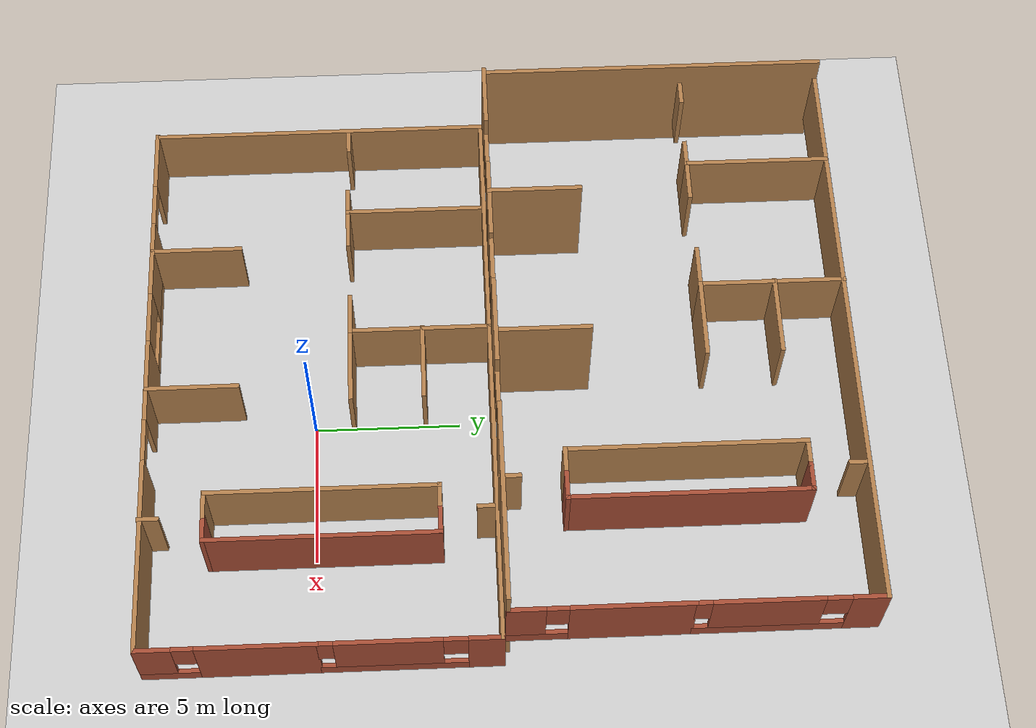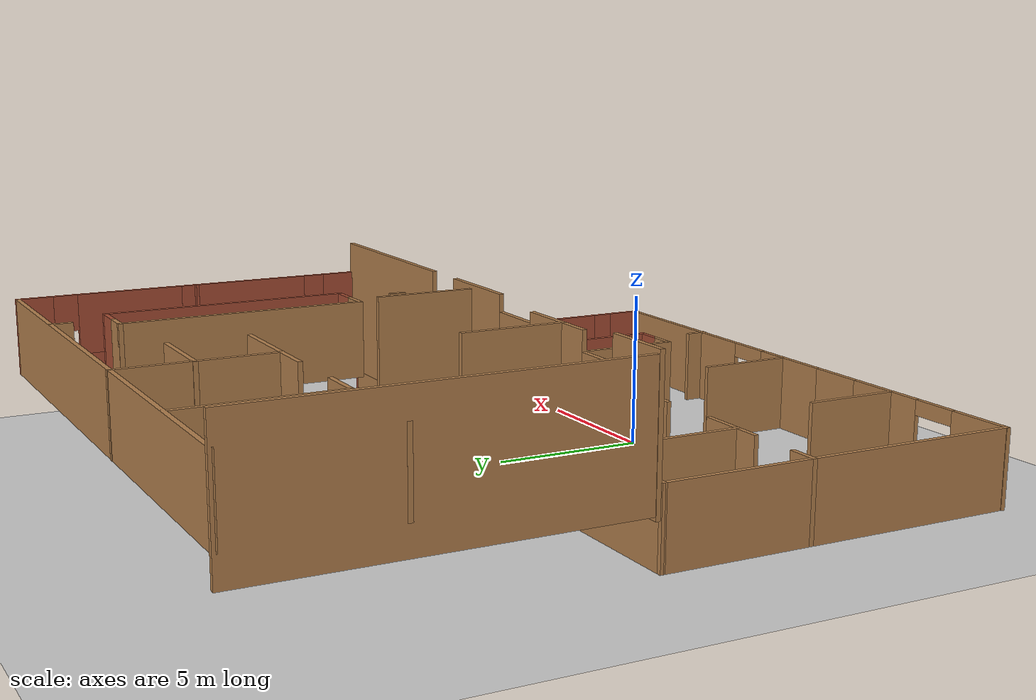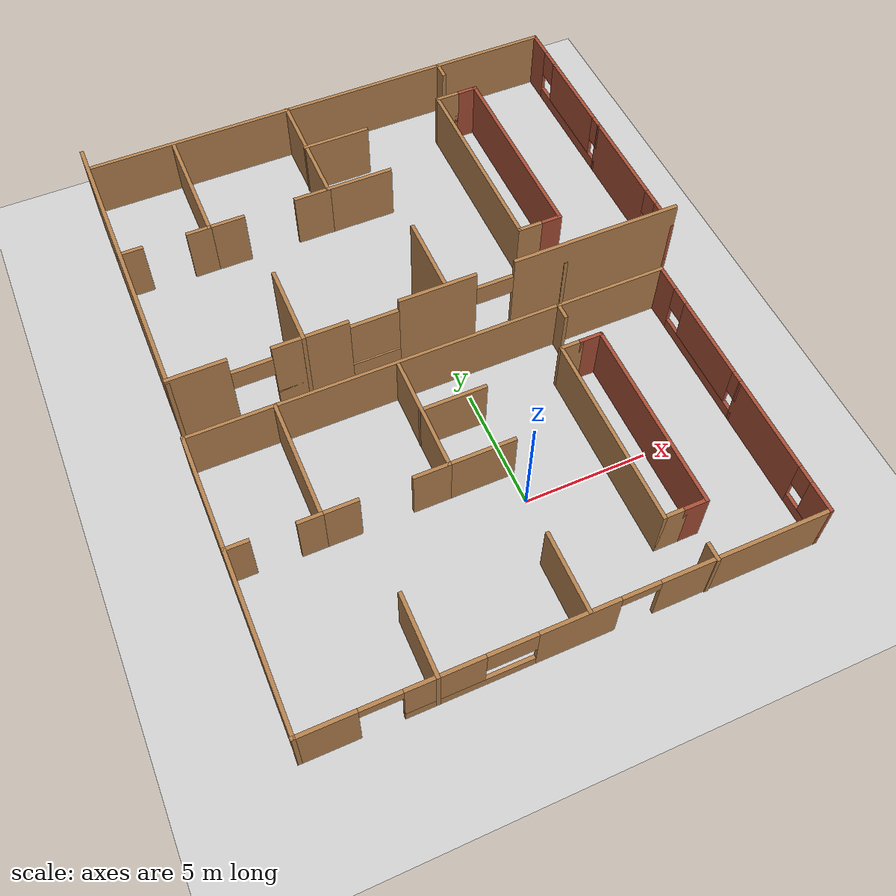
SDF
<sdf version="1.7">
 <world name="default">
  <model name="ground_plane">
   <static>1</static>
   <link name="link">
    <collision name="collision">
     <geometry><plane><normal>0 0 1</normal><size>100 100</size></plane></geometry>
     <surface><friction><ode><mu>100</mu><mu2>50</mu2></ode></friction></surface>
    </collision>
    <visual name="visual">
     <cast_shadows>0</cast_shadows>
     <geometry><plane><normal>0 0 1</normal><size>100 100</size></plane></geometry>
     <material>
      <script><uri>file://media/materials/scripts/gazebo.material</uri><name>Gazebo/Grey</name></script>
     </material>
    </visual>
   </link>
  </model>
  <light name="sun" type="directional">
   <pose>0 0 10 0 -0 0</pose>
   <diffuse>0.8 0.8 0.8 1</diffuse>
   <specular>0.2 0.2 0.2 1</specular>
   <attenuation>
    <range>1000</range>
    <constant>0.9</constant>
    <linear>0.01</linear>
    <quadratic>0.001</quadratic>
   </attenuation>
   <direction>-0.5 0.1 -0.9</direction>
   <spot><inner_angle>0</inner_angle><outer_angle>0</outer_angle><falloff>0</falloff></spot>
  </light>
  <gravity>0 0 -9.8</gravity>
  <magnetic_field>6e-06 2.3e-05 -4.2e-05</magnetic_field>
  <atmosphere type="adiabatic"/>
  <physics type="ode">
   <max_step_size>0.001</max_step_size>
   <real_time_factor>1</real_time_factor>
   <real_time_update_rate>1000</real_time_update_rate>
  </physics>
  <scene><ambient>0.4 0.4 0.4 1</ambient><background>0.7 0.7 0.7 1</background><shadows>1</shadows></scene>
  <audio><device>default</device></audio>
  <spherical_coordinates>
   <surface_model>EARTH_WGS84</surface_model>
   <latitude_deg>0</latitude_deg>
   <longitude_deg>0</longitude_deg>
   <elevation>0</elevation>
   <heading_deg>0</heading_deg>
  </spherical_coordinates>
  <model name="cafe">
   <pose>-1.07181 0.234078 0 0 -0 0</pose>
   <link name="Wall_14">
    <pose>9.93178 -2.98994 0 0 -0 -1.56964</pose>
    <visual name="Wall_14_Visual_0">
     <pose>-0.989557 0 1.25 0 -0 0</pose>
     <geometry><box><size>3.98617 0.15 2.5</size></box></geometry>
     <material>
      <script><uri>file://media/materials/scripts/gazebo.material</uri><name>Gazebo/Bricks</name></script>
      <ambient>1 1 1 1</ambient>
     </material>
     <meta><layer>0</layer></meta>
    </visual>
    <collision name="Wall_14_Collision_0">
     <geometry><box><size>3.98617 0.15 2.5</size></box></geometry>
     <pose>-0.989557 0 1.25 0 -0 0</pose>
    </collision>
    <visual name="Wall_14_Visual_1">
     <pose>1.99308 0 0.25 0 -0 0</pose>
     <geometry><box><size>1.97911 0.15 0.5</size></box></geometry>
     <material>
      <script><uri>file://media/materials/scripts/gazebo.material</uri><name>Gazebo/Bricks</name></script>
      <ambient>1 1 1 1</ambient>
     </material>
     <meta><layer>0</layer></meta>
    </visual>
    <collision name="Wall_14_Collision_1">
     <geometry><box><size>1.97911 0.15 0.5</size></box></geometry>
     <pose>1.99308 0 0.25 0 -0 0</pose>
    </collision>
    <visual name="Wall_14_Visual_2">
     <pose>2.35186 0 1.5 0 -0 0</pose>
     <geometry><box><size>1.26156 0.15 2</size></box></geometry>
     <material>
      <script><uri>file://media/materials/scripts/gazebo.material</uri><name>Gazebo/Bricks</name></script>
      <ambient>1 1 1 1</ambient>
     </material>
     <meta><layer>0</layer></meta>
    </visual>
    <collision name="Wall_14_Collision_2">
     <geometry><box><size>1.26156 0.15 2</size></box></geometry>
     <pose>2.35186 0 1.5 0 -0 0</pose>
    </collision>
    <visual name="Wall_14_Visual_3">
     <pose>1.36231 0 1.9 0 -0 0</pose>
     <geometry><box><size>0.717555 0.15 1.2</size></box></geometry>
     <material>
      <script><uri>file://media/materials/scripts/gazebo.material</uri><name>Gazebo/Bricks</name></script>
      <ambient>1 1 1 1</ambient>
     </material>
     <meta><layer>0</layer></meta>
    </visual>
    <collision name="Wall_14_Collision_3">
     <geometry><box><size>0.717555 0.15 1.2</size></box></geometry>
     <pose>1.36231 0 1.9 0 -0 0</pose>
    </collision>
   </link>
   <link name="Wall_15">
    <pose>-0.010231 -5.89748 0 0 -0 3.14159</pose>
    <visual name="Wall_15_Visual_0">
     <pose>-6.59523 0 1.25 0 -0 0</pose>
     <geometry><box><size>6.80954 0.15 2.5</size></box></geometry>
     <material>
      <script><uri>file://media/materials/scripts/gazebo.material</uri><name>Gazebo/Wood</name></script>
      <ambient>1 1 1 1</ambient>
     </material>
     <meta><layer>0</layer></meta>
    </visual>
    <collision name="Wall_15_Collision_0">
     <geometry><box><size>6.80954 0.15 2.5</size></box></geometry>
     <pose>-6.59523 0 1.25 0 -0 0</pose>
    </collision>
    <visual name="Wall_15_Visual_1">
     <pose>-0.152511 0 1.25 0 -0 0</pose>
     <geometry><box><size>3.07169 0.15 2.5</size></box></geometry>
     <material>
      <script><uri>file://media/materials/scripts/gazebo.material</uri><name>Gazebo/Wood</name></script>
      <ambient>1 1 1 1</ambient>
     </material>
     <meta><layer>0</layer></meta>
    </visual>
    <collision name="Wall_15_Collision_1">
     <geometry><box><size>3.07169 0.15 2.5</size></box></geometry>
     <pose>-0.152511 0 1.25 0 -0 0</pose>
    </collision>
    <visual name="Wall_15_Visual_2">
     <pose>8.87248 0 1.25 0 -0 0</pose>
     <geometry><box><size>2.25504 0.15 2.5</size></box></geometry>
     <material>
      <script><uri>file://media/materials/scripts/gazebo.material</uri><name>Gazebo/Wood</name></script>
      <ambient>1 1 1 1</ambient>
     </material>
     <meta><layer>0</layer></meta>
    </visual>
    <collision name="Wall_15_Collision_2">
     <geometry><box><size>2.25504 0.15 2.5</size></box></geometry>
     <pose>8.87248 0 1.25 0 -0 0</pose>
    </collision>
    <visual name="Wall_15_Visual_3">
     <pose>3.7864 0 0.25 0 -0 0</pose>
     <geometry><box><size>4.80612 0.15 0.5</size></box></geometry>
     <material>
      <script><uri>file://media/materials/scripts/gazebo.material</uri><name>Gazebo/Wood</name></script>
      <ambient>1 1 1 1</ambient>
     </material>
     <meta><layer>0</layer></meta>
    </visual>
    <collision name="Wall_15_Collision_3">
     <geometry><box><size>4.80612 0.15 0.5</size></box></geometry>
     <pose>3.7864 0 0.25 0 -0 0</pose>
    </collision>
    <visual name="Wall_15_Visual_4">
     <pose>4.72994 0 1.5 0 -0 0</pose>
     <geometry><box><size>2.91902 0.15 2</size></box></geometry>
     <material>
      <script><uri>file://media/materials/scripts/gazebo.material</uri><name>Gazebo/Wood</name></script>
      <ambient>1 1 1 1</ambient>
     </material>
     <meta><layer>0</layer></meta>
    </visual>
    <collision name="Wall_15_Collision_4">
     <geometry><box><size>2.91902 0.15 2</size></box></geometry>
     <pose>4.72994 0 1.5 0 -0 0</pose>
    </collision>
    <visual name="Wall_15_Visual_5">
     <pose>2.32688 0 1.9 0 -0 0</pose>
     <geometry><box><size>1.88709 0.15 1.2</size></box></geometry>
     <material>
      <script><uri>file://media/materials/scripts/gazebo.material</uri><name>Gazebo/Wood</name></script>
      <ambient>1 1 1 1</ambient>
     </material>
     <meta><layer>0</layer></meta>
    </visual>
    <collision name="Wall_15_Collision_5">
     <geometry><box><size>1.88709 0.15 1.2</size></box></geometry>
     <pose>2.32688 0 1.9 0 -0 0</pose>
    </collision>
    <visual name="Wall_15_Visual_6">
     <pose>-2.43941 0 2.25 0 -0 0</pose>
     <geometry><box><size>1.5021 0.15 0.5</size></box></geometry>
     <material>
      <script><uri>file://media/materials/scripts/gazebo.material</uri><name>Gazebo/Wood</name></script>
      <ambient>1 1 1 1</ambient>
     </material>
     <meta><layer>0</layer></meta>
    </visual>
    <collision name="Wall_15_Collision_6">
     <geometry><box><size>1.5021 0.15 0.5</size></box></geometry>
     <pose>-2.43941 0 2.25 0 -0 0</pose>
    </collision>
    <visual name="Wall_15_Visual_7">
     <pose>6.9672 0 2.25 0 -0 0</pose>
     <geometry><box><size>1.5555 0.15 0.5</size></box></geometry>
     <material>
      <script><uri>file://media/materials/scripts/gazebo.material</uri><name>Gazebo/Wood</name></script>
      <ambient>1 1 1 1</ambient>
     </material>
     <meta><layer>0</layer></meta>
    </visual>
    <collision name="Wall_15_Collision_7">
     <geometry><box><size>1.5555 0.15 0.5</size></box></geometry>
     <pose>6.9672 0 2.25 0 -0 0</pose>
    </collision>
   </link>
   <link name="Wall_16">
    <collision name="Wall_16_Collision">
     <geometry><box><size>11.9652 0.15 2.5</size></box></geometry>
     <pose>0 0 1.25 0 -0 0</pose>
    </collision>
    <visual name="Wall_16_Visual">
     <pose>0 0 1.25 0 -0 0</pose>
     <geometry><box><size>11.9652 0.15 2.5</size></box></geometry>
     <material>
      <script><uri>file://media/materials/scripts/gazebo.material</uri><name>Gazebo/Wood</name></script>
      <ambient>1 1 1 1</ambient>
     </material>
     <meta><layer>0</layer></meta>
    </visual>
    <pose>-9.91822 0.010065 0 0 -0 1.57137</pose>
   </link>
   <link name="Wall_17">
    <collision name="Wall_17_Collision">
     <geometry><box><size>20 0.15 2.5</size></box></geometry>
     <pose>0 0 1.25 0 -0 0</pose>
    </collision>
    <visual name="Wall_17_Visual">
     <pose>0 0 1.25 0 -0 0</pose>
     <geometry><box><size>20 0.15 2.5</size></box></geometry>
     <material>
      <script><uri>file://media/materials/scripts/gazebo.material</uri><name>Gazebo/Wood</name></script>
      <ambient>1 1 1 1</ambient>
     </material>
     <meta><layer>0</layer></meta>
    </visual>
    <pose>0.003408 5.91761 0 0 -0 0</pose>
   </link>
   <link name="Wall_18">
    <pose>9.92841 2.91761 0 0 -0 -1.5708</pose>
    <visual name="Wall_18_Visual_0">
     <pose>-2.47664 0 1.25 0 -0 0</pose>
     <geometry><box><size>1.19672 0.15 2.5</size></box></geometry>
     <material>
      <script><uri>file://media/materials/scripts/gazebo.material</uri><name>Gazebo/Bricks</name></script>
      <ambient>1 1 1 1</ambient>
     </material>
     <meta><layer>0</layer></meta>
    </visual>
    <collision name="Wall_18_Collision_0">
     <geometry><box><size>1.19672 0.15 2.5</size></box></geometry>
     <pose>-2.47664 0 1.25 0 -0 0</pose>
    </collision>
    <visual name="Wall_18_Visual_1">
     <pose>0.59836 0 0.25 0 -0 0</pose>
     <geometry><box><size>4.95328 0.15 0.5</size></box></geometry>
     <material>
      <script><uri>file://media/materials/scripts/gazebo.material</uri><name>Gazebo/Bricks</name></script>
      <ambient>1 1 1 1</ambient>
     </material>
     <meta><layer>0</layer></meta>
    </visual>
    <collision name="Wall_18_Collision_1">
     <geometry><box><size>4.95328 0.15 0.5</size></box></geometry>
     <pose>0.59836 0 0.25 0 -0 0</pose>
    </collision>
    <visual name="Wall_18_Visual_2">
     <pose>0.693485 0 1.5 0 -0 0</pose>
     <geometry><box><size>3.54353 0.15 2</size></box></geometry>
     <material>
      <script><uri>file://media/materials/scripts/gazebo.material</uri><name>Gazebo/Bricks</name></script>
      <ambient>1 1 1 1</ambient>
     </material>
     <meta><layer>0</layer></meta>
    </visual>
    <collision name="Wall_18_Collision_2">
     <geometry><box><size>3.54353 0.15 2</size></box></geometry>
     <pose>0.693485 0 1.5 0 -0 0</pose>
    </collision>
    <visual name="Wall_18_Visual_3">
     <pose>0.693485 0 1.5 0 -0 0</pose>
     <geometry><box><size>3.54353 0.15 2</size></box></geometry>
     <material>
      <script><uri>file://media/materials/scripts/gazebo.material</uri><name>Gazebo/Bricks</name></script>
      <ambient>1 1 1 1</ambient>
     </material>
     <meta><layer>0</layer></meta>
    </visual>
    <collision name="Wall_18_Collision_3">
     <geometry><box><size>3.54353 0.15 2</size></box></geometry>
     <pose>0.693485 0 1.5 0 -0 0</pose>
    </collision>
    <visual name="Wall_18_Visual_4">
     <pose>-1.47828 0 1.9 0 -0 0</pose>
     <geometry><box><size>0.8 0.15 1.2</size></box></geometry>
     <material>
      <script><uri>file://media/materials/scripts/gazebo.material</uri><name>Gazebo/Bricks</name></script>
      <ambient>1 1 1 1</ambient>
     </material>
     <meta><layer>0</layer></meta>
    </visual>
    <collision name="Wall_18_Collision_4">
     <geometry><box><size>0.8 0.15 1.2</size></box></geometry>
     <pose>-1.47828 0 1.9 0 -0 0</pose>
    </collision>
    <visual name="Wall_18_Visual_5">
     <pose>2.77013 0 1.9 0 -0 0</pose>
     <geometry><box><size>0.60975 0.15 1.2</size></box></geometry>
     <material>
      <script><uri>file://media/materials/scripts/gazebo.material</uri><name>Gazebo/Bricks</name></script>
      <ambient>1 1 1 1</ambient>
     </material>
     <meta><layer>0</layer></meta>
    </visual>
    <collision name="Wall_18_Collision_5">
     <geometry><box><size>0.60975 0.15 1.2</size></box></geometry>
     <pose>2.77013 0 1.9 0 -0 0</pose>
    </collision>
    <visual name="Wall_18_Visual_6">
     <pose>2.77013 0 1.9 0 -0 0</pose>
     <geometry><box><size>0.60975 0.15 1.2</size></box></geometry>
     <material>
      <script><uri>file://media/materials/scripts/gazebo.material</uri><name>Gazebo/Bricks</name></script>
      <ambient>1 1 1 1</ambient>
     </material>
     <meta><layer>0</layer></meta>
    </visual>
    <collision name="Wall_18_Collision_6">
     <geometry><box><size>0.60975 0.15 1.2</size></box></geometry>
     <pose>2.77013 0 1.9 0 -0 0</pose>
    </collision>
   </link>
   <link name="Wall_22">
    <collision name="Wall_22_Collision">
     <geometry><box><size>0.75 0.15 2.5</size></box></geometry>
     <pose>0 0 1.25 0 -0 0</pose>
    </collision>
    <visual name="Wall_22_Visual">
     <pose>0 0 1.25 0 -0 0</pose>
     <geometry><box><size>0.75 0.15 2.5</size></box></geometry>
     <material>
      <script><uri>file://media/materials/scripts/gazebo.material</uri><name>Gazebo/Wood</name></script>
      <ambient>1 1 1 1</ambient>
     </material>
     <meta><layer>0</layer></meta>
    </visual>
    <pose>5.35251 -5.63541 0 0 -0 1.5708</pose>
   </link>
   <link name="Wall_24">
    <collision name="Wall_24_Collision">
     <geometry><box><size>0.75 0.15 2.5</size></box></geometry>
     <pose>0 0 1.25 0 -0 0</pose>
    </collision>
    <visual name="Wall_24_Visual">
     <pose>0 0 1.25 0 -0 0</pose>
     <geometry><box><size>0.75 0.15 2.5</size></box></geometry>
     <material>
      <script><uri>file://media/materials/scripts/gazebo.material</uri><name>Gazebo/Wood</name></script>
      <ambient>1 1 1 1</ambient>
     </material>
     <meta><layer>0</layer></meta>
    </visual>
    <pose>5.31682 5.61552 0 0 -0 -1.5708</pose>
   </link>
   <link name="Wall_26">
    <collision name="Wall_26_Collision">
     <geometry><box><size>5 0.15 2.5</size></box></geometry>
     <pose>0 0 1.25 0 -0 0</pose>
    </collision>
    <visual name="Wall_26_Visual">
     <pose>0 0 1.25 0 -0 0</pose>
     <geometry><box><size>5 0.15 2.5</size></box></geometry>
     <material>
      <script><uri>file://media/materials/scripts/gazebo.material</uri><name>Gazebo/Wood</name></script>
      <ambient>1 1 1 1</ambient>
     </material>
     <meta><layer>0</layer></meta>
    </visual>
    <pose>-6.3931 3.4684 0 0 -0 -1.5708</pose>
   </link>
   <link name="Wall_30">
    <collision name="Wall_30_Collision">
     <geometry><box><size>1 0.15 2.5</size></box></geometry>
     <pose>0 0 1.25 0 -0 0</pose>
    </collision>
    <visual name="Wall_30_Visual">
     <pose>0 0 1.25 0 -0 0</pose>
     <geometry><box><size>1 0.15 2.5</size></box></geometry>
     <material>
      <script><uri>file://media/materials/scripts/gazebo.material</uri><name>Gazebo/Wood</name></script>
      <ambient>1 1 1 1</ambient>
     </material>
     <meta><layer>0</layer></meta>
    </visual>
    <pose>-6.8181 1.0434 0 0 -0 3.14159</pose>
   </link>
   <link name="Wall_34">
    <collision name="Wall_34_Collision">
     <geometry><box><size>1 0.15 2.5</size></box></geometry>
     <pose>0 0 1.25 0 -0 0</pose>
    </collision>
    <visual name="Wall_34_Visual">
     <pose>0 0 1.25 0 -0 0</pose>
     <geometry><box><size>1 0.15 2.5</size></box></geometry>
     <material>
      <script><uri>file://media/materials/scripts/gazebo.material</uri><name>Gazebo/Wood</name></script>
      <ambient>1 1 1 1</ambient>
     </material>
     <meta><layer>0</layer></meta>
    </visual>
    <pose>-9.49428 1.08722 0 0 -0 0</pose>
   </link>
   <link name="Wall_39">
    <collision name="Wall_39_Collision">
     <geometry><box><size>5 0.15 2.5</size></box></geometry>
     <pose>0 0 1.25 0 -0 0</pose>
    </collision>
    <visual name="Wall_39_Visual">
     <pose>0 0 1.25 0 -0 0</pose>
     <geometry><box><size>5 0.15 2.5</size></box></geometry>
     <material>
      <script><uri>file://media/materials/scripts/gazebo.material</uri><name>Gazebo/Wood</name></script>
      <ambient>1 1 1 1</ambient>
     </material>
     <meta><layer>0</layer></meta>
    </visual>
    <pose>-1.50748 3.51041 0 0 -0 -1.5708</pose>
   </link>
   <link name="Wall_40">
    <collision name="Wall_40_Collision">
     <geometry><box><size>1.5 0.15 2.5</size></box></geometry>
     <pose>0 0 1.25 0 -0 0</pose>
    </collision>
    <visual name="Wall_40_Visual">
     <pose>0 0 1.25 0 -0 0</pose>
     <geometry><box><size>1.5 0.15 2.5</size></box></geometry>
     <material>
      <script><uri>file://media/materials/scripts/gazebo.material</uri><name>Gazebo/Wood</name></script>
      <ambient>1 1 1 1</ambient>
     </material>
     <meta><layer>0</layer></meta>
    </visual>
    <pose>-2.18248 1.0854 0 0 -0 3.14159</pose>
   </link>
   <link name="Wall_42">
    <collision name="Wall_42_Collision">
     <geometry><box><size>1.5 0.15 2.5</size></box></geometry>
     <pose>0 0 1.25 0 -0 0</pose>
    </collision>
    <visual name="Wall_42_Visual">
     <pose>0 0 1.25 0 -0 0</pose>
     <geometry><box><size>1.5 0.15 2.5</size></box></geometry>
     <material>
      <script><uri>file://media/materials/scripts/gazebo.material</uri><name>Gazebo/Wood</name></script>
      <ambient>1 1 1 1</ambient>
     </material>
     <meta><layer>0</layer></meta>
    </visual>
    <pose>-5.7181 1.0434 0 0 -0 0</pose>
   </link>
   <link name="Wall_46">
    <collision name="Wall_46_Collision">
     <geometry><box><size>3.25 0.15 2.5</size></box></geometry>
     <pose>0 0 1.25 0 -0 0</pose>
    </collision>
    <visual name="Wall_46_Visual">
     <pose>0 0 1.25 0 -0 0</pose>
     <geometry><box><size>3.25 0.15 2.5</size></box></geometry>
     <material>
      <script><uri>file://media/materials/scripts/gazebo.material</uri><name>Gazebo/Wood</name></script>
      <ambient>1 1 1 1</ambient>
     </material>
     <meta><layer>0</layer></meta>
    </visual>
    <pose>-5.0066 -4.35047 0 0 -0 1.5708</pose>
   </link>
   <link name="Wall_48">
    <collision name="Wall_48_Collision">
     <geometry><box><size>3.25 0.15 2.5</size></box></geometry>
     <pose>0 0 1.25 0 -0 0</pose>
    </collision>
    <visual name="Wall_48_Visual">
     <pose>0 0 1.25 0 -0 0</pose>
     <geometry><box><size>3.25 0.15 2.5</size></box></geometry>
     <material>
      <script><uri>file://media/materials/scripts/gazebo.material</uri><name>Gazebo/Wood</name></script>
      <ambient>1 1 1 1</ambient>
     </material>
     <meta><layer>0</layer></meta>
    </visual>
    <pose>0.491486 -4.33151 0 0 -0 1.5708</pose>
   </link>
   <link name="Wall_55">
    <collision name="Wall_55_Collision">
     <geometry><box><size>1 0.15 2.5</size></box></geometry>
     <pose>0 0 1.25 0 -0 0</pose>
    </collision>
    <visual name="Wall_55_Visual">
     <pose>0 0 1.25 0 -0 0</pose>
     <geometry><box><size>1 0.15 2.5</size></box></geometry>
     <material>
      <script><uri>file://media/materials/scripts/gazebo.material</uri><name>Gazebo/Wood</name></script>
      <ambient>1 1 1 1</ambient>
     </material>
     <meta><layer>0</layer></meta>
    </visual>
    <pose>4.9079 4.0236 0 0 -0 3.14159</pose>
   </link>
   <link name="Wall_56">
    <collision name="Wall_56_Collision">
     <geometry><box><size>8 0.15 2.5</size></box></geometry>
     <pose>0 0 1.25 0 -0 0</pose>
    </collision>
    <visual name="Wall_56_Visual">
     <pose>0 0 1.25 0 -0 0</pose>
     <geometry><box><size>8 0.15 2.5</size></box></geometry>
     <material>
      <script><uri>file://media/materials/scripts/gazebo.material</uri><name>Gazebo/Wood</name></script>
      <ambient>1 1 1 1</ambient>
     </material>
     <meta><layer>0</layer></meta>
    </visual>
    <pose>4.4829 0.098601 0 0 -0 -1.5708</pose>
   </link>
   <link name="Wall_59">
    <collision name="Wall_59_Collision">
     <geometry><box><size>1 0.15 2.5</size></box></geometry>
     <pose>0 0 1.25 0 -0 0</pose>
    </collision>
    <visual name="Wall_59_Visual">
     <pose>0 0 1.25 0 -0 0</pose>
     <geometry><box><size>1 0.15 2.5</size></box></geometry>
     <material>
      <script><uri>file://media/materials/scripts/gazebo.material</uri><name>Gazebo/Wood</name></script>
      <ambient>1 1 1 1</ambient>
     </material>
     <meta><layer>0</layer></meta>
    </visual>
    <pose>4.9079 -3.8264 0 0 -0 0</pose>
   </link>
   <link name="Wall_61">
    <collision name="Wall_61_Collision">
     <geometry><box><size>1 0.15 2.5</size></box></geometry>
     <pose>0 0 1.25 0 -0 0</pose>
    </collision>
    <visual name="Wall_61_Visual">
     <pose>0 0 1.25 0 -0 0</pose>
     <geometry><box><size>1 0.15 2.5</size></box></geometry>
     <material>
      <script><uri>file://media/materials/scripts/gazebo.material</uri><name>Gazebo/Bricks</name></script>
      <ambient>1 1 1 1</ambient>
     </material>
     <meta><layer>0</layer></meta>
    </visual>
    <pose>5.7579 4.0236 0 0 -0 0</pose>
   </link>
   <link name="Wall_62">
    <collision name="Wall_62_Collision">
     <geometry><box><size>8 0.15 2.5</size></box></geometry>
     <pose>0 0 1.25 0 -0 0</pose>
    </collision>
    <visual name="Wall_62_Visual">
     <pose>0 0 1.25 0 -0 0</pose>
     <geometry><box><size>8 0.15 2.5</size></box></geometry>
     <material>
      <script><uri>file://media/materials/scripts/gazebo.material</uri><name>Gazebo/Bricks</name></script>
      <ambient>1 1 1 1</ambient>
     </material>
     <meta><layer>0</layer></meta>
    </visual>
    <pose>6.1829 0.098601 0 0 -0 -1.5708</pose>
   </link>
   <link name="Wall_63">
    <collision name="Wall_63_Collision">
     <geometry><box><size>1 0.15 2.5</size></box></geometry>
     <pose>0 0 1.25 0 -0 0</pose>
    </collision>
    <visual name="Wall_63_Visual">
     <pose>0 0 1.25 0 -0 0</pose>
     <geometry><box><size>1 0.15 2.5</size></box></geometry>
     <material>
      <script><uri>file://media/materials/scripts/gazebo.material</uri><name>Gazebo/Bricks</name></script>
      <ambient>1 1 1 1</ambient>
     </material>
     <meta><layer>0</layer></meta>
    </visual>
    <pose>5.7579 -3.8264 0 0 -0 3.14159</pose>
   </link>
   <link name="Wall_65">
    <collision name="Wall_65_Collision">
     <geometry><box><size>2.75 0.15 2.5</size></box></geometry>
     <pose>0 0 1.25 0 -0 0</pose>
    </collision>
    <visual name="Wall_65_Visual">
     <pose>0 0 1.25 0 -0 0</pose>
     <geometry><box><size>2.75 0.15 2.5</size></box></geometry>
     <material>
      <script><uri>file://media/materials/scripts/gazebo.material</uri><name>Gazebo/Wood</name></script>
      <ambient>1 1 1 1</ambient>
     </material>
     <meta><layer>0</layer></meta>
    </visual>
    <pose>-0.20748 1.0854 0 0 -0 0</pose>
   </link>
   <link name="Wall_67">
    <collision name="Wall_67_Collision">
     <geometry><box><size>2.75 0.15 2.5</size></box></geometry>
     <pose>0 0 1.25 0 -0 0</pose>
    </collision>
    <visual name="Wall_67_Visual">
     <pose>0 0 1.25 0 -0 0</pose>
     <geometry><box><size>2.75 0.15 2.5</size></box></geometry>
     <material>
      <script><uri>file://media/materials/scripts/gazebo.material</uri><name>Gazebo/Wood</name></script>
      <ambient>1 1 1 1</ambient>
     </material>
     <meta><layer>0</layer></meta>
    </visual>
    <pose>-0.229172 3.59219 0 0 -0 0</pose>
   </link>
   <static>1</static>
  </model>
  <model name="cafe_clone">
   <link name="Wall_14">
    <pose>9.93178 -2.98994 0 0 0 -1.56964</pose>
    <visual name="Wall_14_Visual_0">
     <pose>-0.989557 0 1.25 0 -0 0</pose>
     <geometry><box><size>3.98617 0.15 2.5</size></box></geometry>
     <material>
      <script><uri>file://media/materials/scripts/gazebo.material</uri><name>Gazebo/Bricks</name></script>
      <ambient>1 1 1 1</ambient>
      <shader type="pixel"/>
     </material>
     <meta><layer>0</layer></meta>
    </visual>
    <visual name="Wall_14_Visual_1">
     <pose>1.99308 0 0.25 0 -0 0</pose>
     <geometry><box><size>1.97911 0.15 0.5</size></box></geometry>
     <material>
      <script><uri>file://media/materials/scripts/gazebo.material</uri><name>Gazebo/Bricks</name></script>
      <ambient>1 1 1 1</ambient>
      <shader type="pixel"/>
     </material>
     <meta><layer>0</layer></meta>
    </visual>
    <visual name="Wall_14_Visual_2">
     <pose>2.35186 0 1.5 0 -0 0</pose>
     <geometry><box><size>1.26156 0.15 2</size></box></geometry>
     <material>
      <script><uri>file://media/materials/scripts/gazebo.material</uri><name>Gazebo/Bricks</name></script>
      <ambient>1 1 1 1</ambient>
      <shader type="pixel"/>
     </material>
     <meta><layer>0</layer></meta>
    </visual>
    <visual name="Wall_14_Visual_3">
     <pose>1.36231 0 1.9 0 -0 0</pose>
     <geometry><box><size>0.717555 0.15 1.2</size></box></geometry>
     <material>
      <script><uri>file://media/materials/scripts/gazebo.material</uri><name>Gazebo/Bricks</name></script>
      <ambient>1 1 1 1</ambient>
      <shader type="pixel"/>
     </material>
     <meta><layer>0</layer></meta>
    </visual>
    <collision name="Wall_14_Collision_0">
     <pose>-0.989557 0 1.25 0 -0 0</pose>
     <geometry><box><size>3.98617 0.15 2.5</size></box></geometry>
     <surface>
      <friction>
       <ode><mu>1</mu><mu2>1</mu2><fdir1>0 0 0</fdir1><slip1>0</slip1><slip2>0</slip2></ode>
       <torsional>
        <coefficient>1</coefficient>
        <patch_radius>0</patch_radius>
        <surface_radius>0</surface_radius>
        <use_patch_radius>1</use_patch_radius>
        <ode><slip>0</slip></ode>
       </torsional>
      </friction>
      <bounce><restitution_coefficient>0</restitution_coefficient><threshold>1e+06</threshold></bounce>
      <contact>
       <collide_without_contact>0</collide_without_contact>
       <collide_without_contact_bitmask>1</collide_without_contact_bitmask>
       <collide_bitmask>1</collide_bitmask>
       <ode>
        <soft_cfm>0</soft_cfm>
        <soft_erp>0.2</soft_erp>
        <kp>1e+13</kp>
        <kd>1</kd>
        <max_vel>0.01</max_vel>
        <min_depth>0</min_depth>
       </ode>
       <bullet>
        <split_impulse>1</split_impulse>
        <split_impulse_penetration_threshold>-0.01</split_impulse_penetration_threshold>
        <soft_cfm>0</soft_cfm>
        <soft_erp>0.2</soft_erp>
        <kp>1e+13</kp>
        <kd>1</kd>
       </bullet>
      </contact>
     </surface>
    </collision>
    <collision name="Wall_14_Collision_1">
     <pose>1.99308 0 0.25 0 -0 0</pose>
     <geometry><box><size>1.97911 0.15 0.5</size></box></geometry>
     <surface>
      <friction>
       <ode><mu>1</mu><mu2>1</mu2><fdir1>0 0 0</fdir1><slip1>0</slip1><slip2>0</slip2></ode>
       <torsional>
        <coefficient>1</coefficient>
        <patch_radius>0</patch_radius>
        <surface_radius>0</surface_radius>
        <use_patch_radius>1</use_patch_radius>
        <ode><slip>0</slip></ode>
       </torsional>
      </friction>
      <bounce><restitution_coefficient>0</restitution_coefficient><threshold>1e+06</threshold></bounce>
      <contact>
       <collide_without_contact>0</collide_without_contact>
       <collide_without_contact_bitmask>1</collide_without_contact_bitmask>
       <collide_bitmask>1</collide_bitmask>
       <ode>
        <soft_cfm>0</soft_cfm>
        <soft_erp>0.2</soft_erp>
        <kp>1e+13</kp>
        <kd>1</kd>
        <max_vel>0.01</max_vel>
        <min_depth>0</min_depth>
       </ode>
       <bullet>
        <split_impulse>1</split_impulse>
        <split_impulse_penetration_threshold>-0.01</split_impulse_penetration_threshold>
        <soft_cfm>0</soft_cfm>
        <soft_erp>0.2</soft_erp>
        <kp>1e+13</kp>
        <kd>1</kd>
       </bullet>
      </contact>
     </surface>
    </collision>
    <collision name="Wall_14_Collision_2">
     <pose>2.35186 0 1.5 0 -0 0</pose>
     <geometry><box><size>1.26156 0.15 2</size></box></geometry>
     <surface>
      <friction>
       <ode><mu>1</mu><mu2>1</mu2><fdir1>0 0 0</fdir1><slip1>0</slip1><slip2>0</slip2></ode>
       <torsional>
        <coefficient>1</coefficient>
        <patch_radius>0</patch_radius>
        <surface_radius>0</surface_radius>
        <use_patch_radius>1</use_patch_radius>
        <ode><slip>0</slip></ode>
       </torsional>
      </friction>
      <bounce><restitution_coefficient>0</restitution_coefficient><threshold>1e+06</threshold></bounce>
      <contact>
       <collide_without_contact>0</collide_without_contact>
       <collide_without_contact_bitmask>1</collide_without_contact_bitmask>
       <collide_bitmask>1</collide_bitmask>
       <ode>
        <soft_cfm>0</soft_cfm>
        <soft_erp>0.2</soft_erp>
        <kp>1e+13</kp>
        <kd>1</kd>
        <max_vel>0.01</max_vel>
        <min_depth>0</min_depth>
       </ode>
       <bullet>
        <split_impulse>1</split_impulse>
        <split_impulse_penetration_threshold>-0.01</split_impulse_penetration_threshold>
        <soft_cfm>0</soft_cfm>
        <soft_erp>0.2</soft_erp>
        <kp>1e+13</kp>
        <kd>1</kd>
       </bullet>
      </contact>
     </surface>
    </collision>
    <collision name="Wall_14_Collision_3">
     <pose>1.36231 0 1.9 0 -0 0</pose>
     <geometry><box><size>0.717555 0.15 1.2</size></box></geometry>
     <surface>
      <friction>
       <ode><mu>1</mu><mu2>1</mu2><fdir1>0 0 0</fdir1><slip1>0</slip1><slip2>0</slip2></ode>
       <torsional>
        <coefficient>1</coefficient>
        <patch_radius>0</patch_radius>
        <surface_radius>0</surface_radius>
        <use_patch_radius>1</use_patch_radius>
        <ode><slip>0</slip></ode>
       </torsional>
      </friction>
      <bounce><restitution_coefficient>0</restitution_coefficient><threshold>1e+06</threshold></bounce>
      <contact>
       <collide_without_contact>0</collide_without_contact>
       <collide_without_contact_bitmask>1</collide_without_contact_bitmask>
       <collide_bitmask>1</collide_bitmask>
       <ode>
        <soft_cfm>0</soft_cfm>
        <soft_erp>0.2</soft_erp>
        <kp>1e+13</kp>
        <kd>1</kd>
        <max_vel>0.01</max_vel>
        <min_depth>0</min_depth>
       </ode>
       <bullet>
        <split_impulse>1</split_impulse>
        <split_impulse_penetration_threshold>-0.01</split_impulse_penetration_threshold>
        <soft_cfm>0</soft_cfm>
        <soft_erp>0.2</soft_erp>
        <kp>1e+13</kp>
        <kd>1</kd>
       </bullet>
      </contact>
     </surface>
    </collision>
   </link>
   <link name="Wall_15">
    <pose>-0.010231 -5.89748 0 0 -0 3.14159</pose>
    <inertial>
     <inertia><ixx>0</ixx><ixy>0</ixy><ixz>0</ixz><iyy>0</iyy><iyz>0</iyz><izz>0</izz></inertia>
     <mass>0</mass>
    </inertial>
    <visual name="Wall_15_Visual_1">
     <pose>-0.152511 0 1.25 0 -0 0</pose>
     <geometry><box><size>3.07169 0.15 4.54997</size></box></geometry>
     <material>
      <script><uri>file://media/materials/scripts/gazebo.material</uri><name>Gazebo/Wood</name></script>
      <ambient>1 1 1 1</ambient>
      <shader type="pixel"/>
     </material>
     <meta><layer>0</layer></meta>
    </visual>
    <visual name="Wall_15_Visual_0">
     <pose>-6.59523 0 1.25 0 -0 0</pose>
     <geometry><box><size>6.80954 0.15 4.54997</size></box></geometry>
     <material>
      <script><uri>file://media/materials/scripts/gazebo.material</uri><name>Gazebo/Wood</name></script>
      <ambient>1 1 1 1</ambient>
      <shader type="pixel"/>
     </material>
     <meta><layer>0</layer></meta>
    </visual>
    <visual name="Wall_15_Visual_2">
     <pose>8.87248 0 1.25 0 -0 0</pose>
     <geometry><box><size>2.25504 0.15 4.54997</size></box></geometry>
     <material>
      <script><uri>file://media/materials/scripts/gazebo.material</uri><name>Gazebo/Wood</name></script>
      <ambient>1 1 1 1</ambient>
      <shader type="pixel"/>
     </material>
     <meta><layer>0</layer></meta>
    </visual>
    <visual name="Wall_15_Visual_3">
     <pose>3.7864 0 0.25 0 -0 0</pose>
     <geometry><box><size>4.80612 0.15 0.909994</size></box></geometry>
     <material>
      <script><uri>file://media/materials/scripts/gazebo.material</uri><name>Gazebo/Wood</name></script>
      <ambient>1 1 1 1</ambient>
      <shader type="pixel"/>
     </material>
     <meta><layer>0</layer></meta>
    </visual>
    <visual name="Wall_15_Visual_4">
     <pose>4.72994 0 1.5 0 -0 0</pose>
     <geometry><box><size>2.91902 0.15 3.63997</size></box></geometry>
     <material>
      <script><uri>file://media/materials/scripts/gazebo.material</uri><name>Gazebo/Wood</name></script>
      <ambient>1 1 1 1</ambient>
      <shader type="pixel"/>
     </material>
     <meta><layer>0</layer></meta>
    </visual>
    <visual name="Wall_15_Visual_5">
     <pose>2.32688 0 1.9 0 -0 0</pose>
     <geometry><box><size>1.88709 0.15 2.18398</size></box></geometry>
     <material>
      <script><uri>file://media/materials/scripts/gazebo.material</uri><name>Gazebo/Wood</name></script>
      <ambient>1 1 1 1</ambient>
      <shader type="pixel"/>
     </material>
     <meta><layer>0</layer></meta>
    </visual>
    <visual name="Wall_15_Visual_6">
     <pose>-2.43941 0 2.25 0 -0 0</pose>
     <geometry><box><size>1.5021 0.15 0.909994</size></box></geometry>
     <material>
      <script><uri>file://media/materials/scripts/gazebo.material</uri><name>Gazebo/Wood</name></script>
      <ambient>1 1 1 1</ambient>
      <shader type="pixel"/>
     </material>
     <meta><layer>0</layer></meta>
    </visual>
    <visual name="Wall_15_Visual_7">
     <pose>6.9672 0 2.25 0 -0 0</pose>
     <geometry><box><size>1.5555 0.15 0.909994</size></box></geometry>
     <material>
      <script><uri>file://media/materials/scripts/gazebo.material</uri><name>Gazebo/Wood</name></script>
      <ambient>1 1 1 1</ambient>
      <shader type="pixel"/>
     </material>
     <meta><layer>0</layer></meta>
    </visual>
    <collision name="Wall_15_Collision_0">
     <pose>-6.59523 0 1.25 0 -0 0</pose>
     <geometry><box><size>6.80954 0.15 4.54997</size></box></geometry>
     <surface>
      <friction>
       <ode><mu>1</mu><mu2>1</mu2><fdir1>0 0 0</fdir1><slip1>0</slip1><slip2>0</slip2></ode>
       <torsional>
        <coefficient>1</coefficient>
        <patch_radius>0</patch_radius>
        <surface_radius>0</surface_radius>
        <use_patch_radius>1</use_patch_radius>
        <ode><slip>0</slip></ode>
       </torsional>
      </friction>
      <bounce><restitution_coefficient>0</restitution_coefficient><threshold>1e+06</threshold></bounce>
      <contact>
       <collide_without_contact>0</collide_without_contact>
       <collide_without_contact_bitmask>1</collide_without_contact_bitmask>
       <collide_bitmask>1</collide_bitmask>
       <ode>
        <soft_cfm>0</soft_cfm>
        <soft_erp>0.2</soft_erp>
        <kp>1e+13</kp>
        <kd>1</kd>
        <max_vel>0.01</max_vel>
        <min_depth>0</min_depth>
       </ode>
       <bullet>
        <split_impulse>1</split_impulse>
        <split_impulse_penetration_threshold>-0.01</split_impulse_penetration_threshold>
        <soft_cfm>0</soft_cfm>
        <soft_erp>0.2</soft_erp>
        <kp>1e+13</kp>
        <kd>1</kd>
       </bullet>
      </contact>
     </surface>
    </collision>
    <collision name="Wall_15_Collision_1">
     <pose>-0.152511 0 1.25 0 -0 0</pose>
     <geometry><box><size>3.07169 0.15 4.54997</size></box></geometry>
     <surface>
      <friction>
       <ode><mu>1</mu><mu2>1</mu2><fdir1>0 0 0</fdir1><slip1>0</slip1><slip2>0</slip2></ode>
       <torsional>
        <coefficient>1</coefficient>
        <patch_radius>0</patch_radius>
        <surface_radius>0</surface_radius>
        <use_patch_radius>1</use_patch_radius>
        <ode><slip>0</slip></ode>
       </torsional>
      </friction>
      <bounce><restitution_coefficient>0</restitution_coefficient><threshold>1e+06</threshold></bounce>
      <contact>
       <collide_without_contact>0</collide_without_contact>
       <collide_without_contact_bitmask>1</collide_without_contact_bitmask>
       <collide_bitmask>1</collide_bitmask>
       <ode>
        <soft_cfm>0</soft_cfm>
        <soft_erp>0.2</soft_erp>
        <kp>1e+13</kp>
        <kd>1</kd>
        <max_vel>0.01</max_vel>
        <min_depth>0</min_depth>
       </ode>
       <bullet>
        <split_impulse>1</split_impulse>
        <split_impulse_penetration_threshold>-0.01</split_impulse_penetration_threshold>
        <soft_cfm>0</soft_cfm>
        <soft_erp>0.2</soft_erp>
        <kp>1e+13</kp>
        <kd>1</kd>
       </bullet>
      </contact>
     </surface>
    </collision>
    <collision name="Wall_15_Collision_2">
     <pose>8.87248 0 1.25 0 -0 0</pose>
     <geometry><box><size>2.25504 0.15 4.54997</size></box></geometry>
     <surface>
      <friction>
       <ode><mu>1</mu><mu2>1</mu2><fdir1>0 0 0</fdir1><slip1>0</slip1><slip2>0</slip2></ode>
       <torsional>
        <coefficient>1</coefficient>
        <patch_radius>0</patch_radius>
        <surface_radius>0</surface_radius>
        <use_patch_radius>1</use_patch_radius>
        <ode><slip>0</slip></ode>
       </torsional>
      </friction>
      <bounce><restitution_coefficient>0</restitution_coefficient><threshold>1e+06</threshold></bounce>
      <contact>
       <collide_without_contact>0</collide_without_contact>
       <collide_without_contact_bitmask>1</collide_without_contact_bitmask>
       <collide_bitmask>1</collide_bitmask>
       <ode>
        <soft_cfm>0</soft_cfm>
        <soft_erp>0.2</soft_erp>
        <kp>1e+13</kp>
        <kd>1</kd>
        <max_vel>0.01</max_vel>
        <min_depth>0</min_depth>
       </ode>
       <bullet>
        <split_impulse>1</split_impulse>
        <split_impulse_penetration_threshold>-0.01</split_impulse_penetration_threshold>
        <soft_cfm>0</soft_cfm>
        <soft_erp>0.2</soft_erp>
        <kp>1e+13</kp>
        <kd>1</kd>
       </bullet>
      </contact>
     </surface>
    </collision>
    <collision name="Wall_15_Collision_3">
     <pose>3.7864 0 0.25 0 -0 0</pose>
     <geometry><box><size>4.80612 0.15 0.909994</size></box></geometry>
     <surface>
      <friction>
       <ode><mu>1</mu><mu2>1</mu2><fdir1>0 0 0</fdir1><slip1>0</slip1><slip2>0</slip2></ode>
       <torsional>
        <coefficient>1</coefficient>
        <patch_radius>0</patch_radius>
        <surface_radius>0</surface_radius>
        <use_patch_radius>1</use_patch_radius>
        <ode><slip>0</slip></ode>
       </torsional>
      </friction>
      <bounce><restitution_coefficient>0</restitution_coefficient><threshold>1e+06</threshold></bounce>
      <contact>
       <collide_without_contact>0</collide_without_contact>
       <collide_without_contact_bitmask>1</collide_without_contact_bitmask>
       <collide_bitmask>1</collide_bitmask>
       <ode>
        <soft_cfm>0</soft_cfm>
        <soft_erp>0.2</soft_erp>
        <kp>1e+13</kp>
        <kd>1</kd>
        <max_vel>0.01</max_vel>
        <min_depth>0</min_depth>
       </ode>
       <bullet>
        <split_impulse>1</split_impulse>
        <split_impulse_penetration_threshold>-0.01</split_impulse_penetration_threshold>
        <soft_cfm>0</soft_cfm>
        <soft_erp>0.2</soft_erp>
        <kp>1e+13</kp>
        <kd>1</kd>
       </bullet>
      </contact>
     </surface>
    </collision>
    <collision name="Wall_15_Collision_4">
     <pose>4.72994 0 1.5 0 -0 0</pose>
     <geometry><box><size>2.91902 0.15 3.63997</size></box></geometry>
     <surface>
      <friction>
       <ode><mu>1</mu><mu2>1</mu2><fdir1>0 0 0</fdir1><slip1>0</slip1><slip2>0</slip2></ode>
       <torsional>
        <coefficient>1</coefficient>
        <patch_radius>0</patch_radius>
        <surface_radius>0</surface_radius>
        <use_patch_radius>1</use_patch_radius>
        <ode><slip>0</slip></ode>
       </torsional>
      </friction>
      <bounce><restitution_coefficient>0</restitution_coefficient><threshold>1e+06</threshold></bounce>
      <contact>
       <collide_without_contact>0</collide_without_contact>
       <collide_without_contact_bitmask>1</collide_without_contact_bitmask>
       <collide_bitmask>1</collide_bitmask>
       <ode>
        <soft_cfm>0</soft_cfm>
        <soft_erp>0.2</soft_erp>
        <kp>1e+13</kp>
        <kd>1</kd>
        <max_vel>0.01</max_vel>
        <min_depth>0</min_depth>
       </ode>
       <bullet>
        <split_impulse>1</split_impulse>
        <split_impulse_penetration_threshold>-0.01</split_impulse_penetration_threshold>
        <soft_cfm>0</soft_cfm>
        <soft_erp>0.2</soft_erp>
        <kp>1e+13</kp>
        <kd>1</kd>
       </bullet>
      </contact>
     </surface>
    </collision>
    <collision name="Wall_15_Collision_5">
     <pose>2.32688 0 1.9 0 -0 0</pose>
     <geometry><box><size>1.88709 0.15 2.18398</size></box></geometry>
     <surface>
      <friction>
       <ode><mu>1</mu><mu2>1</mu2><fdir1>0 0 0</fdir1><slip1>0</slip1><slip2>0</slip2></ode>
       <torsional>
        <coefficient>1</coefficient>
        <patch_radius>0</patch_radius>
        <surface_radius>0</surface_radius>
        <use_patch_radius>1</use_patch_radius>
        <ode><slip>0</slip></ode>
       </torsional>
      </friction>
      <bounce><restitution_coefficient>0</restitution_coefficient><threshold>1e+06</threshold></bounce>
      <contact>
       <collide_without_contact>0</collide_without_contact>
       <collide_without_contact_bitmask>1</collide_without_contact_bitmask>
       <collide_bitmask>1</collide_bitmask>
       <ode>
        <soft_cfm>0</soft_cfm>
        <soft_erp>0.2</soft_erp>
        <kp>1e+13</kp>
        <kd>1</kd>
        <max_vel>0.01</max_vel>
        <min_depth>0</min_depth>
       </ode>
       <bullet>
        <split_impulse>1</split_impulse>
        <split_impulse_penetration_threshold>-0.01</split_impulse_penetration_threshold>
        <soft_cfm>0</soft_cfm>
        <soft_erp>0.2</soft_erp>
        <kp>1e+13</kp>
        <kd>1</kd>
       </bullet>
      </contact>
     </surface>
    </collision>
    <collision name="Wall_15_Collision_6">
     <pose>-2.43941 0 2.25 0 -0 0</pose>
     <geometry><box><size>1.5021 0.15 0.909994</size></box></geometry>
     <surface>
      <friction>
       <ode><mu>1</mu><mu2>1</mu2><fdir1>0 0 0</fdir1><slip1>0</slip1><slip2>0</slip2></ode>
       <torsional>
        <coefficient>1</coefficient>
        <patch_radius>0</patch_radius>
        <surface_radius>0</surface_radius>
        <use_patch_radius>1</use_patch_radius>
        <ode><slip>0</slip></ode>
       </torsional>
      </friction>
      <bounce><restitution_coefficient>0</restitution_coefficient><threshold>1e+06</threshold></bounce>
      <contact>
       <collide_without_contact>0</collide_without_contact>
       <collide_without_contact_bitmask>1</collide_without_contact_bitmask>
       <collide_bitmask>1</collide_bitmask>
       <ode>
        <soft_cfm>0</soft_cfm>
        <soft_erp>0.2</soft_erp>
        <kp>1e+13</kp>
        <kd>1</kd>
        <max_vel>0.01</max_vel>
        <min_depth>0</min_depth>
       </ode>
       <bullet>
        <split_impulse>1</split_impulse>
        <split_impulse_penetration_threshold>-0.01</split_impulse_penetration_threshold>
        <soft_cfm>0</soft_cfm>
        <soft_erp>0.2</soft_erp>
        <kp>1e+13</kp>
        <kd>1</kd>
       </bullet>
      </contact>
     </surface>
    </collision>
    <collision name="Wall_15_Collision_7">
     <pose>6.9672 0 2.25 0 -0 0</pose>
     <geometry><box><size>1.5555 0.15 0.909994</size></box></geometry>
     <surface>
      <friction>
       <ode><mu>1</mu><mu2>1</mu2><fdir1>0 0 0</fdir1><slip1>0</slip1><slip2>0</slip2></ode>
       <torsional>
        <coefficient>1</coefficient>
        <patch_radius>0</patch_radius>
        <surface_radius>0</surface_radius>
        <use_patch_radius>1</use_patch_radius>
        <ode><slip>0</slip></ode>
       </torsional>
      </friction>
      <bounce><restitution_coefficient>0</restitution_coefficient><threshold>1e+06</threshold></bounce>
      <contact>
       <collide_without_contact>0</collide_without_contact>
       <collide_without_contact_bitmask>1</collide_without_contact_bitmask>
       <collide_bitmask>1</collide_bitmask>
       <ode>
        <soft_cfm>0</soft_cfm>
        <soft_erp>0.2</soft_erp>
        <kp>1e+13</kp>
        <kd>1</kd>
        <max_vel>0.01</max_vel>
        <min_depth>0</min_depth>
       </ode>
       <bullet>
        <split_impulse>1</split_impulse>
        <split_impulse_penetration_threshold>-0.01</split_impulse_penetration_threshold>
        <soft_cfm>0</soft_cfm>
        <soft_erp>0.2</soft_erp>
        <kp>1e+13</kp>
        <kd>1</kd>
       </bullet>
      </contact>
     </surface>
    </collision>
   </link>
   <link name="Wall_16">
    <pose>-9.91822 0.010065 0 0 -0 1.57137</pose>
    <inertial>
     <inertia><ixx>0</ixx><ixy>0</ixy><ixz>0</ixz><iyy>0</iyy><iyz>0</iyz><izz>0</izz></inertia>
     <mass>0</mass>
    </inertial>
    <visual name="Wall_16_Visual">
     <pose>0 0 1.25 0 -0 0</pose>
     <geometry><box><size>11.9652 0.15 4.29563</size></box></geometry>
     <material>
      <script><uri>file://media/materials/scripts/gazebo.material</uri><name>Gazebo/Wood</name></script>
      <ambient>1 1 1 1</ambient>
      <shader type="pixel"/>
     </material>
     <meta><layer>0</layer></meta>
    </visual>
    <collision name="Wall_16_Collision">
     <pose>0 0 1.25 0 -0 0</pose>
     <geometry><box><size>11.9652 0.15 4.29563</size></box></geometry>
     <surface>
      <friction>
       <ode><mu>1</mu><mu2>1</mu2><fdir1>0 0 0</fdir1><slip1>0</slip1><slip2>0</slip2></ode>
       <torsional>
        <coefficient>1</coefficient>
        <patch_radius>0</patch_radius>
        <surface_radius>0</surface_radius>
        <use_patch_radius>1</use_patch_radius>
        <ode><slip>0</slip></ode>
       </torsional>
      </friction>
      <bounce><restitution_coefficient>0</restitution_coefficient><threshold>1e+06</threshold></bounce>
      <contact>
       <collide_without_contact>0</collide_without_contact>
       <collide_without_contact_bitmask>1</collide_without_contact_bitmask>
       <collide_bitmask>1</collide_bitmask>
       <ode>
        <soft_cfm>0</soft_cfm>
        <soft_erp>0.2</soft_erp>
        <kp>1e+13</kp>
        <kd>1</kd>
        <max_vel>0.01</max_vel>
        <min_depth>0</min_depth>
       </ode>
       <bullet>
        <split_impulse>1</split_impulse>
        <split_impulse_penetration_threshold>-0.01</split_impulse_penetration_threshold>
        <soft_cfm>0</soft_cfm>
        <soft_erp>0.2</soft_erp>
        <kp>1e+13</kp>
        <kd>1</kd>
       </bullet>
      </contact>
     </surface>
    </collision>
   </link>
   <link name="Wall_17">
    <pose>0.003408 5.91761 0 0 -0 0</pose>
    <visual name="Wall_17_Visual">
     <pose>0 0 1.25 0 -0 0</pose>
     <geometry><box><size>20 0.15 2.5</size></box></geometry>
     <material>
      <script><uri>file://media/materials/scripts/gazebo.material</uri><name>Gazebo/Wood</name></script>
      <ambient>1 1 1 1</ambient>
      <shader type="pixel"/>
     </material>
     <meta><layer>0</layer></meta>
    </visual>
    <collision name="Wall_17_Collision">
     <pose>0 0 1.25 0 -0 0</pose>
     <geometry><box><size>20 0.15 2.5</size></box></geometry>
     <surface>
      <friction>
       <ode><mu>1</mu><mu2>1</mu2><fdir1>0 0 0</fdir1><slip1>0</slip1><slip2>0</slip2></ode>
       <torsional>
        <coefficient>1</coefficient>
        <patch_radius>0</patch_radius>
        <surface_radius>0</surface_radius>
        <use_patch_radius>1</use_patch_radius>
        <ode><slip>0</slip></ode>
       </torsional>
      </friction>
      <bounce><restitution_coefficient>0</restitution_coefficient><threshold>1e+06</threshold></bounce>
      <contact>
       <collide_without_contact>0</collide_without_contact>
       <collide_without_contact_bitmask>1</collide_without_contact_bitmask>
       <collide_bitmask>1</collide_bitmask>
       <ode>
        <soft_cfm>0</soft_cfm>
        <soft_erp>0.2</soft_erp>
        <kp>1e+13</kp>
        <kd>1</kd>
        <max_vel>0.01</max_vel>
        <min_depth>0</min_depth>
       </ode>
       <bullet>
        <split_impulse>1</split_impulse>
        <split_impulse_penetration_threshold>-0.01</split_impulse_penetration_threshold>
        <soft_cfm>0</soft_cfm>
        <soft_erp>0.2</soft_erp>
        <kp>1e+13</kp>
        <kd>1</kd>
       </bullet>
      </contact>
     </surface>
    </collision>
   </link>
   <link name="Wall_18">
    <pose>9.92841 2.91761 0 0 0 -1.5708</pose>
    <visual name="Wall_18_Visual_0">
     <pose>-2.47664 0 1.25 0 -0 0</pose>
     <geometry><box><size>1.19672 0.15 2.5</size></box></geometry>
     <material>
      <script><uri>file://media/materials/scripts/gazebo.material</uri><name>Gazebo/Bricks</name></script>
      <ambient>1 1 1 1</ambient>
      <shader type="pixel"/>
     </material>
     <meta><layer>0</layer></meta>
    </visual>
    <visual name="Wall_18_Visual_1">
     <pose>0.59836 0 0.25 0 -0 0</pose>
     <geometry><box><size>4.95328 0.15 0.5</size></box></geometry>
     <material>
      <script><uri>file://media/materials/scripts/gazebo.material</uri><name>Gazebo/Bricks</name></script>
      <ambient>1 1 1 1</ambient>
      <shader type="pixel"/>
     </material>
     <meta><layer>0</layer></meta>
    </visual>
    <visual name="Wall_18_Visual_2">
     <pose>0.693485 0 1.5 0 -0 0</pose>
     <geometry><box><size>3.54353 0.15 2</size></box></geometry>
     <material>
      <script><uri>file://media/materials/scripts/gazebo.material</uri><name>Gazebo/Bricks</name></script>
      <ambient>1 1 1 1</ambient>
      <shader type="pixel"/>
     </material>
     <meta><layer>0</layer></meta>
    </visual>
    <visual name="Wall_18_Visual_3">
     <pose>0.693485 0 1.5 0 -0 0</pose>
     <geometry><box><size>3.54353 0.15 2</size></box></geometry>
     <material>
      <script><uri>file://media/materials/scripts/gazebo.material</uri><name>Gazebo/Bricks</name></script>
      <ambient>1 1 1 1</ambient>
      <shader type="pixel"/>
     </material>
     <meta><layer>0</layer></meta>
    </visual>
    <visual name="Wall_18_Visual_4">
     <pose>-1.47828 0 1.9 0 -0 0</pose>
     <geometry><box><size>0.8 0.15 1.2</size></box></geometry>
     <material>
      <script><uri>file://media/materials/scripts/gazebo.material</uri><name>Gazebo/Bricks</name></script>
      <ambient>1 1 1 1</ambient>
      <shader type="pixel"/>
     </material>
     <meta><layer>0</layer></meta>
    </visual>
    <visual name="Wall_18_Visual_5">
     <pose>2.77013 0 1.9 0 -0 0</pose>
     <geometry><box><size>0.60975 0.15 1.2</size></box></geometry>
     <material>
      <script><uri>file://media/materials/scripts/gazebo.material</uri><name>Gazebo/Bricks</name></script>
      <ambient>1 1 1 1</ambient>
      <shader type="pixel"/>
     </material>
     <meta><layer>0</layer></meta>
    </visual>
    <visual name="Wall_18_Visual_6">
     <pose>2.77013 0 1.9 0 -0 0</pose>
     <geometry><box><size>0.60975 0.15 1.2</size></box></geometry>
     <material>
      <script><uri>file://media/materials/scripts/gazebo.material</uri><name>Gazebo/Bricks</name></script>
      <ambient>1 1 1 1</ambient>
      <shader type="pixel"/>
     </material>
     <meta><layer>0</layer></meta>
    </visual>
    <collision name="Wall_18_Collision_0">
     <pose>-2.47664 0 1.25 0 -0 0</pose>
     <geometry><box><size>1.19672 0.15 2.5</size></box></geometry>
     <surface>
      <friction>
       <ode><mu>1</mu><mu2>1</mu2><fdir1>0 0 0</fdir1><slip1>0</slip1><slip2>0</slip2></ode>
       <torsional>
        <coefficient>1</coefficient>
        <patch_radius>0</patch_radius>
        <surface_radius>0</surface_radius>
        <use_patch_radius>1</use_patch_radius>
        <ode><slip>0</slip></ode>
       </torsional>
      </friction>
      <bounce><restitution_coefficient>0</restitution_coefficient><threshold>1e+06</threshold></bounce>
      <contact>
       <collide_without_contact>0</collide_without_contact>
       <collide_without_contact_bitmask>1</collide_without_contact_bitmask>
       <collide_bitmask>1</collide_bitmask>
       <ode>
        <soft_cfm>0</soft_cfm>
        <soft_erp>0.2</soft_erp>
        <kp>1e+13</kp>
        <kd>1</kd>
        <max_vel>0.01</max_vel>
        <min_depth>0</min_depth>
       </ode>
       <bullet>
        <split_impulse>1</split_impulse>
        <split_impulse_penetration_threshold>-0.01</split_impulse_penetration_threshold>
        <soft_cfm>0</soft_cfm>
        <soft_erp>0.2</soft_erp>
        <kp>1e+13</kp>
        <kd>1</kd>
       </bullet>
      </contact>
     </surface>
    </collision>
    <collision name="Wall_18_Collision_1">
     <pose>0.59836 0 0.25 0 -0 0</pose>
     <geometry><box><size>4.95328 0.15 0.5</size></box></geometry>
     <surface>
      <friction>
       <ode><mu>1</mu><mu2>1</mu2><fdir1>0 0 0</fdir1><slip1>0</slip1><slip2>0</slip2></ode>
       <torsional>
        <coefficient>1</coefficient>
        <patch_radius>0</patch_radius>
        <surface_radius>0</surface_radius>
        <use_patch_radius>1</use_patch_radius>
        <ode><slip>0</slip></ode>
       </torsional>
      </friction>
      <bounce><restitution_coefficient>0</restitution_coefficient><threshold>1e+06</threshold></bounce>
      <contact>
       <collide_without_contact>0</collide_without_contact>
       <collide_without_contact_bitmask>1</collide_without_contact_bitmask>
       <collide_bitmask>1</collide_bitmask>
       <ode>
        <soft_cfm>0</soft_cfm>
        <soft_erp>0.2</soft_erp>
        <kp>1e+13</kp>
        <kd>1</kd>
        <max_vel>0.01</max_vel>
        <min_depth>0</min_depth>
       </ode>
       <bullet>
        <split_impulse>1</split_impulse>
        <split_impulse_penetration_threshold>-0.01</split_impulse_penetration_threshold>
        <soft_cfm>0</soft_cfm>
        <soft_erp>0.2</soft_erp>
        <kp>1e+13</kp>
        <kd>1</kd>
       </bullet>
      </contact>
     </surface>
    </collision>
    <collision name="Wall_18_Collision_2">
     <pose>0.693485 0 1.5 0 -0 0</pose>
     <geometry><box><size>3.54353 0.15 2</size></box></geometry>
     <surface>
      <friction>
       <ode><mu>1</mu><mu2>1</mu2><fdir1>0 0 0</fdir1><slip1>0</slip1><slip2>0</slip2></ode>
       <torsional>
        <coefficient>1</coefficient>
        <patch_radius>0</patch_radius>
        <surface_radius>0</surface_radius>
        <use_patch_radius>1</use_patch_radius>
        <ode><slip>0</slip></ode>
       </torsional>
      </friction>
      <bounce><restitution_coefficient>0</restitution_coefficient><threshold>1e+06</threshold></bounce>
      <contact>
       <collide_without_contact>0</collide_without_contact>
       <collide_without_contact_bitmask>1</collide_without_contact_bitmask>
       <collide_bitmask>1</collide_bitmask>
       <ode>
        <soft_cfm>0</soft_cfm>
        <soft_erp>0.2</soft_erp>
        <kp>1e+13</kp>
        <kd>1</kd>
        <max_vel>0.01</max_vel>
        <min_depth>0</min_depth>
       </ode>
       <bullet>
        <split_impulse>1</split_impulse>
        <split_impulse_penetration_threshold>-0.01</split_impulse_penetration_threshold>
        <soft_cfm>0</soft_cfm>
        <soft_erp>0.2</soft_erp>
        <kp>1e+13</kp>
        <kd>1</kd>
       </bullet>
      </contact>
     </surface>
    </collision>
    <collision name="Wall_18_Collision_3">
     <pose>0.693485 0 1.5 0 -0 0</pose>
     <geometry><box><size>3.54353 0.15 2</size></box></geometry>
     <surface>
      <friction>
       <ode><mu>1</mu><mu2>1</mu2><fdir1>0 0 0</fdir1><slip1>0</slip1><slip2>0</slip2></ode>
       <torsional>
        <coefficient>1</coefficient>
        <patch_radius>0</patch_radius>
        <surface_radius>0</surface_radius>
        <use_patch_radius>1</use_patch_radius>
        <ode><slip>0</slip></ode>
       </torsional>
      </friction>
      <bounce><restitution_coefficient>0</restitution_coefficient><threshold>1e+06</threshold></bounce>
      <contact>
       <collide_without_contact>0</collide_without_contact>
       <collide_without_contact_bitmask>1</collide_without_contact_bitmask>
       <collide_bitmask>1</collide_bitmask>
       <ode>
        <soft_cfm>0</soft_cfm>
        <soft_erp>0.2</soft_erp>
        <kp>1e+13</kp>
        <kd>1</kd>
        <max_vel>0.01</max_vel>
        <min_depth>0</min_depth>
       </ode>
       <bullet>
        <split_impulse>1</split_impulse>
        <split_impulse_penetration_threshold>-0.01</split_impulse_penetration_threshold>
        <soft_cfm>0</soft_cfm>
        <soft_erp>0.2</soft_erp>
        <kp>1e+13</kp>
        <kd>1</kd>
       </bullet>
      </contact>
     </surface>
    </collision>
    <collision name="Wall_18_Collision_5">
     <pose>2.77013 0 1.9 0 -0 0</pose>
     <geometry><box><size>0.60975 0.15 1.2</size></box></geometry>
     <surface>
      <friction>
       <ode><mu>1</mu><mu2>1</mu2><fdir1>0 0 0</fdir1><slip1>0</slip1><slip2>0</slip2></ode>
       <torsional>
        <coefficient>1</coefficient>
        <patch_radius>0</patch_radius>
        <surface_radius>0</surface_radius>
        <use_patch_radius>1</use_patch_radius>
        <ode><slip>0</slip></ode>
       </torsional>
      </friction>
      <bounce><restitution_coefficient>0</restitution_coefficient><threshold>1e+06</threshold></bounce>
      <contact>
       <collide_without_contact>0</collide_without_contact>
       <collide_without_contact_bitmask>1</collide_without_contact_bitmask>
       <collide_bitmask>1</collide_bitmask>
       <ode>
        <soft_cfm>0</soft_cfm>
        <soft_erp>0.2</soft_erp>
        <kp>1e+13</kp>
        <kd>1</kd>
        <max_vel>0.01</max_vel>
        <min_depth>0</min_depth>
       </ode>
       <bullet>
        <split_impulse>1</split_impulse>
        <split_impulse_penetration_threshold>-0.01</split_impulse_penetration_threshold>
        <soft_cfm>0</soft_cfm>
        <soft_erp>0.2</soft_erp>
        <kp>1e+13</kp>
        <kd>1</kd>
       </bullet>
      </contact>
     </surface>
    </collision>
    <collision name="Wall_18_Collision_4">
     <pose>-1.47828 0 1.9 0 -0 0</pose>
     <geometry><box><size>0.8 0.15 1.2</size></box></geometry>
     <surface>
      <friction>
       <ode><mu>1</mu><mu2>1</mu2><fdir1>0 0 0</fdir1><slip1>0</slip1><slip2>0</slip2></ode>
       <torsional>
        <coefficient>1</coefficient>
        <patch_radius>0</patch_radius>
        <surface_radius>0</surface_radius>
        <use_patch_radius>1</use_patch_radius>
        <ode><slip>0</slip></ode>
       </torsional>
      </friction>
      <bounce><restitution_coefficient>0</restitution_coefficient><threshold>1e+06</threshold></bounce>
      <contact>
       <collide_without_contact>0</collide_without_contact>
       <collide_without_contact_bitmask>1</collide_without_contact_bitmask>
       <collide_bitmask>1</collide_bitmask>
       <ode>
        <soft_cfm>0</soft_cfm>
        <soft_erp>0.2</soft_erp>
        <kp>1e+13</kp>
        <kd>1</kd>
        <max_vel>0.01</max_vel>
        <min_depth>0</min_depth>
       </ode>
       <bullet>
        <split_impulse>1</split_impulse>
        <split_impulse_penetration_threshold>-0.01</split_impulse_penetration_threshold>
        <soft_cfm>0</soft_cfm>
        <soft_erp>0.2</soft_erp>
        <kp>1e+13</kp>
        <kd>1</kd>
       </bullet>
      </contact>
     </surface>
    </collision>
    <collision name="Wall_18_Collision_6">
     <pose>2.77013 0 1.9 0 -0 0</pose>
     <geometry><box><size>0.60975 0.15 1.2</size></box></geometry>
     <surface>
      <friction>
       <ode><mu>1</mu><mu2>1</mu2><fdir1>0 0 0</fdir1><slip1>0</slip1><slip2>0</slip2></ode>
       <torsional>
        <coefficient>1</coefficient>
        <patch_radius>0</patch_radius>
        <surface_radius>0</surface_radius>
        <use_patch_radius>1</use_patch_radius>
        <ode><slip>0</slip></ode>
       </torsional>
      </friction>
      <bounce><restitution_coefficient>0</restitution_coefficient><threshold>1e+06</threshold></bounce>
      <contact>
       <collide_without_contact>0</collide_without_contact>
       <collide_without_contact_bitmask>1</collide_without_contact_bitmask>
       <collide_bitmask>1</collide_bitmask>
       <ode>
        <soft_cfm>0</soft_cfm>
        <soft_erp>0.2</soft_erp>
        <kp>1e+13</kp>
        <kd>1</kd>
        <max_vel>0.01</max_vel>
        <min_depth>0</min_depth>
       </ode>
       <bullet>
        <split_impulse>1</split_impulse>
        <split_impulse_penetration_threshold>-0.01</split_impulse_penetration_threshold>
        <soft_cfm>0</soft_cfm>
        <soft_erp>0.2</soft_erp>
        <kp>1e+13</kp>
        <kd>1</kd>
       </bullet>
      </contact>
     </surface>
    </collision>
   </link>
   <link name="Wall_22">
    <pose>5.35251 -5.63541 0 0 -0 1.5708</pose>
    <visual name="Wall_22_Visual">
     <pose>0 0 1.25 0 -0 0</pose>
     <geometry><box><size>0.75 0.15 2.5</size></box></geometry>
     <material>
      <script><uri>file://media/materials/scripts/gazebo.material</uri><name>Gazebo/Wood</name></script>
      <ambient>1 1 1 1</ambient>
      <shader type="pixel"/>
     </material>
     <meta><layer>0</layer></meta>
    </visual>
    <collision name="Wall_22_Collision">
     <pose>0 0 1.25 0 -0 0</pose>
     <geometry><box><size>0.75 0.15 2.5</size></box></geometry>
     <surface>
      <friction>
       <ode><mu>1</mu><mu2>1</mu2><fdir1>0 0 0</fdir1><slip1>0</slip1><slip2>0</slip2></ode>
       <torsional>
        <coefficient>1</coefficient>
        <patch_radius>0</patch_radius>
        <surface_radius>0</surface_radius>
        <use_patch_radius>1</use_patch_radius>
        <ode><slip>0</slip></ode>
       </torsional>
      </friction>
      <bounce><restitution_coefficient>0</restitution_coefficient><threshold>1e+06</threshold></bounce>
      <contact>
       <collide_without_contact>0</collide_without_contact>
       <collide_without_contact_bitmask>1</collide_without_contact_bitmask>
       <collide_bitmask>1</collide_bitmask>
       <ode>
        <soft_cfm>0</soft_cfm>
        <soft_erp>0.2</soft_erp>
        <kp>1e+13</kp>
        <kd>1</kd>
        <max_vel>0.01</max_vel>
        <min_depth>0</min_depth>
       </ode>
       <bullet>
        <split_impulse>1</split_impulse>
        <split_impulse_penetration_threshold>-0.01</split_impulse_penetration_threshold>
        <soft_cfm>0</soft_cfm>
        <soft_erp>0.2</soft_erp>
        <kp>1e+13</kp>
        <kd>1</kd>
       </bullet>
      </contact>
     </surface>
    </collision>
   </link>
   <link name="Wall_24">
    <pose>5.31682 5.61552 0 0 0 -1.5708</pose>
    <visual name="Wall_24_Visual">
     <pose>0 0 1.25 0 -0 0</pose>
     <geometry><box><size>0.75 0.15 2.5</size></box></geometry>
     <material>
      <script><uri>file://media/materials/scripts/gazebo.material</uri><name>Gazebo/Wood</name></script>
      <ambient>1 1 1 1</ambient>
      <shader type="pixel"/>
     </material>
     <meta><layer>0</layer></meta>
    </visual>
    <collision name="Wall_24_Collision">
     <pose>0 0 1.25 0 -0 0</pose>
     <geometry><box><size>0.75 0.15 2.5</size></box></geometry>
     <surface>
      <friction>
       <ode><mu>1</mu><mu2>1</mu2><fdir1>0 0 0</fdir1><slip1>0</slip1><slip2>0</slip2></ode>
       <torsional>
        <coefficient>1</coefficient>
        <patch_radius>0</patch_radius>
        <surface_radius>0</surface_radius>
        <use_patch_radius>1</use_patch_radius>
        <ode><slip>0</slip></ode>
       </torsional>
      </friction>
      <bounce><restitution_coefficient>0</restitution_coefficient><threshold>1e+06</threshold></bounce>
      <contact>
       <collide_without_contact>0</collide_without_contact>
       <collide_without_contact_bitmask>1</collide_without_contact_bitmask>
       <collide_bitmask>1</collide_bitmask>
       <ode>
        <soft_cfm>0</soft_cfm>
        <soft_erp>0.2</soft_erp>
        <kp>1e+13</kp>
        <kd>1</kd>
        <max_vel>0.01</max_vel>
        <min_depth>0</min_depth>
       </ode>
       <bullet>
        <split_impulse>1</split_impulse>
        <split_impulse_penetration_threshold>-0.01</split_impulse_penetration_threshold>
        <soft_cfm>0</soft_cfm>
        <soft_erp>0.2</soft_erp>
        <kp>1e+13</kp>
        <kd>1</kd>
       </bullet>
      </contact>
     </surface>
    </collision>
   </link>
   <link name="Wall_26">
    <pose>-6.3931 3.4684 0 0 0 -1.5708</pose>
    <visual name="Wall_26_Visual">
     <pose>0 0 1.25 0 -0 0</pose>
     <geometry><box><size>5 0.15 2.5</size></box></geometry>
     <material>
      <script><uri>file://media/materials/scripts/gazebo.material</uri><name>Gazebo/Wood</name></script>
      <ambient>1 1 1 1</ambient>
      <shader type="pixel"/>
     </material>
     <meta><layer>0</layer></meta>
    </visual>
    <collision name="Wall_26_Collision">
     <pose>0 0 1.25 0 -0 0</pose>
     <geometry><box><size>5 0.15 2.5</size></box></geometry>
     <surface>
      <friction>
       <ode><mu>1</mu><mu2>1</mu2><fdir1>0 0 0</fdir1><slip1>0</slip1><slip2>0</slip2></ode>
       <torsional>
        <coefficient>1</coefficient>
        <patch_radius>0</patch_radius>
        <surface_radius>0</surface_radius>
        <use_patch_radius>1</use_patch_radius>
        <ode><slip>0</slip></ode>
       </torsional>
      </friction>
      <bounce><restitution_coefficient>0</restitution_coefficient><threshold>1e+06</threshold></bounce>
      <contact>
       <collide_without_contact>0</collide_without_contact>
       <collide_without_contact_bitmask>1</collide_without_contact_bitmask>
       <collide_bitmask>1</collide_bitmask>
       <ode>
        <soft_cfm>0</soft_cfm>
        <soft_erp>0.2</soft_erp>
        <kp>1e+13</kp>
        <kd>1</kd>
        <max_vel>0.01</max_vel>
        <min_depth>0</min_depth>
       </ode>
       <bullet>
        <split_impulse>1</split_impulse>
        <split_impulse_penetration_threshold>-0.01</split_impulse_penetration_threshold>
        <soft_cfm>0</soft_cfm>
        <soft_erp>0.2</soft_erp>
        <kp>1e+13</kp>
        <kd>1</kd>
       </bullet>
      </contact>
     </surface>
    </collision>
   </link>
   <link name="Wall_30">
    <pose>-6.8181 1.0434 0 0 -0 3.14159</pose>
    <visual name="Wall_30_Visual">
     <pose>0 0 1.25 0 -0 0</pose>
     <geometry><box><size>1 0.15 2.5</size></box></geometry>
     <material>
      <script><uri>file://media/materials/scripts/gazebo.material</uri><name>Gazebo/Wood</name></script>
      <ambient>1 1 1 1</ambient>
      <shader type="pixel"/>
     </material>
     <meta><layer>0</layer></meta>
    </visual>
    <collision name="Wall_30_Collision">
     <pose>0 0 1.25 0 -0 0</pose>
     <geometry><box><size>1 0.15 2.5</size></box></geometry>
     <surface>
      <friction>
       <ode><mu>1</mu><mu2>1</mu2><fdir1>0 0 0</fdir1><slip1>0</slip1><slip2>0</slip2></ode>
       <torsional>
        <coefficient>1</coefficient>
        <patch_radius>0</patch_radius>
        <surface_radius>0</surface_radius>
        <use_patch_radius>1</use_patch_radius>
        <ode><slip>0</slip></ode>
       </torsional>
      </friction>
      <bounce><restitution_coefficient>0</restitution_coefficient><threshold>1e+06</threshold></bounce>
      <contact>
       <collide_without_contact>0</collide_without_contact>
       <collide_without_contact_bitmask>1</collide_without_contact_bitmask>
       <collide_bitmask>1</collide_bitmask>
       <ode>
        <soft_cfm>0</soft_cfm>
        <soft_erp>0.2</soft_erp>
        <kp>1e+13</kp>
        <kd>1</kd>
        <max_vel>0.01</max_vel>
        <min_depth>0</min_depth>
       </ode>
       <bullet>
        <split_impulse>1</split_impulse>
        <split_impulse_penetration_threshold>-0.01</split_impulse_penetration_threshold>
        <soft_cfm>0</soft_cfm>
        <soft_erp>0.2</soft_erp>
        <kp>1e+13</kp>
        <kd>1</kd>
       </bullet>
      </contact>
     </surface>
    </collision>
   </link>
   <link name="Wall_34">
    <pose>-9.49428 1.08722 0 0 -0 0</pose>
    <visual name="Wall_34_Visual">
     <pose>0 0 1.25 0 -0 0</pose>
     <geometry><box><size>1 0.15 2.5</size></box></geometry>
     <material>
      <script><uri>file://media/materials/scripts/gazebo.material</uri><name>Gazebo/Wood</name></script>
      <ambient>1 1 1 1</ambient>
      <shader type="pixel"/>
     </material>
     <meta><layer>0</layer></meta>
    </visual>
    <collision name="Wall_34_Collision">
     <pose>0 0 1.25 0 -0 0</pose>
     <geometry><box><size>1 0.15 2.5</size></box></geometry>
     <surface>
      <friction>
       <ode><mu>1</mu><mu2>1</mu2><fdir1>0 0 0</fdir1><slip1>0</slip1><slip2>0</slip2></ode>
       <torsional>
        <coefficient>1</coefficient>
        <patch_radius>0</patch_radius>
        <surface_radius>0</surface_radius>
        <use_patch_radius>1</use_patch_radius>
        <ode><slip>0</slip></ode>
       </torsional>
      </friction>
      <bounce><restitution_coefficient>0</restitution_coefficient><threshold>1e+06</threshold></bounce>
      <contact>
       <collide_without_contact>0</collide_without_contact>
       <collide_without_contact_bitmask>1</collide_without_contact_bitmask>
       <collide_bitmask>1</collide_bitmask>
       <ode>
        <soft_cfm>0</soft_cfm>
        <soft_erp>0.2</soft_erp>
        <kp>1e+13</kp>
        <kd>1</kd>
        <max_vel>0.01</max_vel>
        <min_depth>0</min_depth>
       </ode>
       <bullet>
        <split_impulse>1</split_impulse>
        <split_impulse_penetration_threshold>-0.01</split_impulse_penetration_threshold>
        <soft_cfm>0</soft_cfm>
        <soft_erp>0.2</soft_erp>
        <kp>1e+13</kp>
        <kd>1</kd>
       </bullet>
      </contact>
     </surface>
    </collision>
   </link>
   <link name="Wall_39">
    <pose>-1.50748 3.51041 0 0 0 -1.5708</pose>
    <visual name="Wall_39_Visual">
     <pose>0 0 1.25 0 -0 0</pose>
     <geometry><box><size>5 0.15 2.5</size></box></geometry>
     <material>
      <script><uri>file://media/materials/scripts/gazebo.material</uri><name>Gazebo/Wood</name></script>
      <ambient>1 1 1 1</ambient>
      <shader type="pixel"/>
     </material>
     <meta><layer>0</layer></meta>
    </visual>
    <collision name="Wall_39_Collision">
     <pose>0 0 1.25 0 -0 0</pose>
     <geometry><box><size>5 0.15 2.5</size></box></geometry>
     <surface>
      <friction>
       <ode><mu>1</mu><mu2>1</mu2><fdir1>0 0 0</fdir1><slip1>0</slip1><slip2>0</slip2></ode>
       <torsional>
        <coefficient>1</coefficient>
        <patch_radius>0</patch_radius>
        <surface_radius>0</surface_radius>
        <use_patch_radius>1</use_patch_radius>
        <ode><slip>0</slip></ode>
       </torsional>
      </friction>
      <bounce><restitution_coefficient>0</restitution_coefficient><threshold>1e+06</threshold></bounce>
      <contact>
       <collide_without_contact>0</collide_without_contact>
       <collide_without_contact_bitmask>1</collide_without_contact_bitmask>
       <collide_bitmask>1</collide_bitmask>
       <ode>
        <soft_cfm>0</soft_cfm>
        <soft_erp>0.2</soft_erp>
        <kp>1e+13</kp>
        <kd>1</kd>
        <max_vel>0.01</max_vel>
        <min_depth>0</min_depth>
       </ode>
       <bullet>
        <split_impulse>1</split_impulse>
        <split_impulse_penetration_threshold>-0.01</split_impulse_penetration_threshold>
        <soft_cfm>0</soft_cfm>
        <soft_erp>0.2</soft_erp>
        <kp>1e+13</kp>
        <kd>1</kd>
       </bullet>
      </contact>
     </surface>
    </collision>
   </link>
   <link name="Wall_40">
    <pose>-2.18248 1.0854 0 0 -0 3.14159</pose>
    <visual name="Wall_40_Visual">
     <pose>0 0 1.25 0 -0 0</pose>
     <geometry><box><size>1.5 0.15 2.5</size></box></geometry>
     <material>
      <script><uri>file://media/materials/scripts/gazebo.material</uri><name>Gazebo/Wood</name></script>
      <ambient>1 1 1 1</ambient>
      <shader type="pixel"/>
     </material>
     <meta><layer>0</layer></meta>
    </visual>
    <collision name="Wall_40_Collision">
     <pose>0 0 1.25 0 -0 0</pose>
     <geometry><box><size>1.5 0.15 2.5</size></box></geometry>
     <surface>
      <friction>
       <ode><mu>1</mu><mu2>1</mu2><fdir1>0 0 0</fdir1><slip1>0</slip1><slip2>0</slip2></ode>
       <torsional>
        <coefficient>1</coefficient>
        <patch_radius>0</patch_radius>
        <surface_radius>0</surface_radius>
        <use_patch_radius>1</use_patch_radius>
        <ode><slip>0</slip></ode>
       </torsional>
      </friction>
      <bounce><restitution_coefficient>0</restitution_coefficient><threshold>1e+06</threshold></bounce>
      <contact>
       <collide_without_contact>0</collide_without_contact>
       <collide_without_contact_bitmask>1</collide_without_contact_bitmask>
       <collide_bitmask>1</collide_bitmask>
       <ode>
        <soft_cfm>0</soft_cfm>
        <soft_erp>0.2</soft_erp>
        <kp>1e+13</kp>
        <kd>1</kd>
        <max_vel>0.01</max_vel>
        <min_depth>0</min_depth>
       </ode>
       <bullet>
        <split_impulse>1</split_impulse>
        <split_impulse_penetration_threshold>-0.01</split_impulse_penetration_threshold>
        <soft_cfm>0</soft_cfm>
        <soft_erp>0.2</soft_erp>
        <kp>1e+13</kp>
        <kd>1</kd>
       </bullet>
      </contact>
     </surface>
    </collision>
   </link>
   <link name="Wall_42">
    <pose>-5.7181 1.0434 0 0 -0 0</pose>
    <visual name="Wall_42_Visual">
     <pose>0 0 1.25 0 -0 0</pose>
     <geometry><box><size>1.5 0.15 2.5</size></box></geometry>
     <material>
      <script><uri>file://media/materials/scripts/gazebo.material</uri><name>Gazebo/Wood</name></script>
      <ambient>1 1 1 1</ambient>
      <shader type="pixel"/>
     </material>
     <meta><layer>0</layer></meta>
    </visual>
    <collision name="Wall_42_Collision">
     <pose>0 0 1.25 0 -0 0</pose>
     <geometry><box><size>1.5 0.15 2.5</size></box></geometry>
     <surface>
      <friction>
       <ode><mu>1</mu><mu2>1</mu2><fdir1>0 0 0</fdir1><slip1>0</slip1><slip2>0</slip2></ode>
       <torsional>
        <coefficient>1</coefficient>
        <patch_radius>0</patch_radius>
        <surface_radius>0</surface_radius>
        <use_patch_radius>1</use_patch_radius>
        <ode><slip>0</slip></ode>
       </torsional>
      </friction>
      <bounce><restitution_coefficient>0</restitution_coefficient><threshold>1e+06</threshold></bounce>
      <contact>
       <collide_without_contact>0</collide_without_contact>
       <collide_without_contact_bitmask>1</collide_without_contact_bitmask>
       <collide_bitmask>1</collide_bitmask>
       <ode>
        <soft_cfm>0</soft_cfm>
        <soft_erp>0.2</soft_erp>
        <kp>1e+13</kp>
        <kd>1</kd>
        <max_vel>0.01</max_vel>
        <min_depth>0</min_depth>
       </ode>
       <bullet>
        <split_impulse>1</split_impulse>
        <split_impulse_penetration_threshold>-0.01</split_impulse_penetration_threshold>
        <soft_cfm>0</soft_cfm>
        <soft_erp>0.2</soft_erp>
        <kp>1e+13</kp>
        <kd>1</kd>
       </bullet>
      </contact>
     </surface>
    </collision>
   </link>
   <link name="Wall_46">
    <pose>-5.0066 -4.35047 0 0 -0 1.5708</pose>
    <inertial>
     <inertia><ixx>0</ixx><ixy>0</ixy><ixz>0</ixz><iyy>0</iyy><iyz>0</iyz><izz>0</izz></inertia>
     <mass>0</mass>
    </inertial>
    <visual name="Wall_46_Visual">
     <pose>0 0 1.25 0 -0 0</pose>
     <geometry><box><size>3.25 0.15 4.14194</size></box></geometry>
     <material>
      <script><uri>file://media/materials/scripts/gazebo.material</uri><name>Gazebo/Wood</name></script>
      <ambient>1 1 1 1</ambient>
      <shader type="pixel"/>
     </material>
     <meta><layer>0</layer></meta>
    </visual>
    <collision name="Wall_46_Collision">
     <pose>0 0 1.25 0 -0 0</pose>
     <geometry><box><size>3.25 0.15 4.14194</size></box></geometry>
     <surface>
      <friction>
       <ode><mu>1</mu><mu2>1</mu2><fdir1>0 0 0</fdir1><slip1>0</slip1><slip2>0</slip2></ode>
       <torsional>
        <coefficient>1</coefficient>
        <patch_radius>0</patch_radius>
        <surface_radius>0</surface_radius>
        <use_patch_radius>1</use_patch_radius>
        <ode><slip>0</slip></ode>
       </torsional>
      </friction>
      <bounce><restitution_coefficient>0</restitution_coefficient><threshold>1e+06</threshold></bounce>
      <contact>
       <collide_without_contact>0</collide_without_contact>
       <collide_without_contact_bitmask>1</collide_without_contact_bitmask>
       <collide_bitmask>1</collide_bitmask>
       <ode>
        <soft_cfm>0</soft_cfm>
        <soft_erp>0.2</soft_erp>
        <kp>1e+13</kp>
        <kd>1</kd>
        <max_vel>0.01</max_vel>
        <min_depth>0</min_depth>
       </ode>
       <bullet>
        <split_impulse>1</split_impulse>
        <split_impulse_penetration_threshold>-0.01</split_impulse_penetration_threshold>
        <soft_cfm>0</soft_cfm>
        <soft_erp>0.2</soft_erp>
        <kp>1e+13</kp>
        <kd>1</kd>
       </bullet>
      </contact>
     </surface>
    </collision>
   </link>
   <link name="Wall_48">
    <pose>0.491486 -4.33151 0 0 -0 1.5708</pose>
    <inertial>
     <inertia><ixx>0</ixx><ixy>0</ixy><ixz>0</ixz><iyy>0</iyy><iyz>0</iyz><izz>0</izz></inertia>
     <mass>0</mass>
    </inertial>
    <visual name="Wall_48_Visual">
     <pose>0 0 1.25 0 -0 0</pose>
     <geometry><box><size>3.25 0.15 4.29503</size></box></geometry>
     <material>
      <script><uri>file://media/materials/scripts/gazebo.material</uri><name>Gazebo/Wood</name></script>
      <ambient>1 1 1 1</ambient>
      <shader type="pixel"/>
     </material>
     <meta><layer>0</layer></meta>
    </visual>
    <collision name="Wall_48_Collision">
     <pose>0 0 1.25 0 -0 0</pose>
     <geometry><box><size>3.25 0.15 4.29503</size></box></geometry>
     <surface>
      <friction>
       <ode><mu>1</mu><mu2>1</mu2><fdir1>0 0 0</fdir1><slip1>0</slip1><slip2>0</slip2></ode>
       <torsional>
        <coefficient>1</coefficient>
        <patch_radius>0</patch_radius>
        <surface_radius>0</surface_radius>
        <use_patch_radius>1</use_patch_radius>
        <ode><slip>0</slip></ode>
       </torsional>
      </friction>
      <bounce><restitution_coefficient>0</restitution_coefficient><threshold>1e+06</threshold></bounce>
      <contact>
       <collide_without_contact>0</collide_without_contact>
       <collide_without_contact_bitmask>1</collide_without_contact_bitmask>
       <collide_bitmask>1</collide_bitmask>
       <ode>
        <soft_cfm>0</soft_cfm>
        <soft_erp>0.2</soft_erp>
        <kp>1e+13</kp>
        <kd>1</kd>
        <max_vel>0.01</max_vel>
        <min_depth>0</min_depth>
       </ode>
       <bullet>
        <split_impulse>1</split_impulse>
        <split_impulse_penetration_threshold>-0.01</split_impulse_penetration_threshold>
        <soft_cfm>0</soft_cfm>
        <soft_erp>0.2</soft_erp>
        <kp>1e+13</kp>
        <kd>1</kd>
       </bullet>
      </contact>
     </surface>
    </collision>
   </link>
   <link name="Wall_55">
    <pose>4.9079 4.0236 0 0 -0 3.14159</pose>
    <visual name="Wall_55_Visual">
     <pose>0 0 1.25 0 -0 0</pose>
     <geometry><box><size>1 0.15 2.5</size></box></geometry>
     <material>
      <script><uri>file://media/materials/scripts/gazebo.material</uri><name>Gazebo/Wood</name></script>
      <ambient>1 1 1 1</ambient>
      <shader type="pixel"/>
     </material>
     <meta><layer>0</layer></meta>
    </visual>
    <collision name="Wall_55_Collision">
     <pose>0 0 1.25 0 -0 0</pose>
     <geometry><box><size>1 0.15 2.5</size></box></geometry>
     <surface>
      <friction>
       <ode><mu>1</mu><mu2>1</mu2><fdir1>0 0 0</fdir1><slip1>0</slip1><slip2>0</slip2></ode>
       <torsional>
        <coefficient>1</coefficient>
        <patch_radius>0</patch_radius>
        <surface_radius>0</surface_radius>
        <use_patch_radius>1</use_patch_radius>
        <ode><slip>0</slip></ode>
       </torsional>
      </friction>
      <bounce><restitution_coefficient>0</restitution_coefficient><threshold>1e+06</threshold></bounce>
      <contact>
       <collide_without_contact>0</collide_without_contact>
       <collide_without_contact_bitmask>1</collide_without_contact_bitmask>
       <collide_bitmask>1</collide_bitmask>
       <ode>
        <soft_cfm>0</soft_cfm>
        <soft_erp>0.2</soft_erp>
        <kp>1e+13</kp>
        <kd>1</kd>
        <max_vel>0.01</max_vel>
        <min_depth>0</min_depth>
       </ode>
       <bullet>
        <split_impulse>1</split_impulse>
        <split_impulse_penetration_threshold>-0.01</split_impulse_penetration_threshold>
        <soft_cfm>0</soft_cfm>
        <soft_erp>0.2</soft_erp>
        <kp>1e+13</kp>
        <kd>1</kd>
       </bullet>
      </contact>
     </surface>
    </collision>
   </link>
   <link name="Wall_56">
    <pose>4.4829 0.098601 0 0 0 -1.5708</pose>
    <visual name="Wall_56_Visual">
     <pose>0 0 1.25 0 -0 0</pose>
     <geometry><box><size>8 0.15 2.5</size></box></geometry>
     <material>
      <script><uri>file://media/materials/scripts/gazebo.material</uri><name>Gazebo/Wood</name></script>
      <ambient>1 1 1 1</ambient>
      <shader type="pixel"/>
     </material>
     <meta><layer>0</layer></meta>
    </visual>
    <collision name="Wall_56_Collision">
     <pose>0 0 1.25 0 -0 0</pose>
     <geometry><box><size>8 0.15 2.5</size></box></geometry>
     <surface>
      <friction>
       <ode><mu>1</mu><mu2>1</mu2><fdir1>0 0 0</fdir1><slip1>0</slip1><slip2>0</slip2></ode>
       <torsional>
        <coefficient>1</coefficient>
        <patch_radius>0</patch_radius>
        <surface_radius>0</surface_radius>
        <use_patch_radius>1</use_patch_radius>
        <ode><slip>0</slip></ode>
       </torsional>
      </friction>
      <bounce><restitution_coefficient>0</restitution_coefficient><threshold>1e+06</threshold></bounce>
      <contact>
       <collide_without_contact>0</collide_without_contact>
       <collide_without_contact_bitmask>1</collide_without_contact_bitmask>
       <collide_bitmask>1</collide_bitmask>
       <ode>
        <soft_cfm>0</soft_cfm>
        <soft_erp>0.2</soft_erp>
        <kp>1e+13</kp>
        <kd>1</kd>
        <max_vel>0.01</max_vel>
        <min_depth>0</min_depth>
       </ode>
       <bullet>
        <split_impulse>1</split_impulse>
        <split_impulse_penetration_threshold>-0.01</split_impulse_penetration_threshold>
        <soft_cfm>0</soft_cfm>
        <soft_erp>0.2</soft_erp>
        <kp>1e+13</kp>
        <kd>1</kd>
       </bullet>
      </contact>
     </surface>
    </collision>
   </link>
   <link name="Wall_59">
    <pose>4.9079 -3.8264 0 0 -0 0</pose>
    <visual name="Wall_59_Visual">
     <pose>0 0 1.25 0 -0 0</pose>
     <geometry><box><size>1 0.15 2.5</size></box></geometry>
     <material>
      <script><uri>file://media/materials/scripts/gazebo.material</uri><name>Gazebo/Wood</name></script>
      <ambient>1 1 1 1</ambient>
      <shader type="pixel"/>
     </material>
     <meta><layer>0</layer></meta>
    </visual>
    <collision name="Wall_59_Collision">
     <pose>0 0 1.25 0 -0 0</pose>
     <geometry><box><size>1 0.15 2.5</size></box></geometry>
     <surface>
      <friction>
       <ode><mu>1</mu><mu2>1</mu2><fdir1>0 0 0</fdir1><slip1>0</slip1><slip2>0</slip2></ode>
       <torsional>
        <coefficient>1</coefficient>
        <patch_radius>0</patch_radius>
        <surface_radius>0</surface_radius>
        <use_patch_radius>1</use_patch_radius>
        <ode><slip>0</slip></ode>
       </torsional>
      </friction>
      <bounce><restitution_coefficient>0</restitution_coefficient><threshold>1e+06</threshold></bounce>
      <contact>
       <collide_without_contact>0</collide_without_contact>
       <collide_without_contact_bitmask>1</collide_without_contact_bitmask>
       <collide_bitmask>1</collide_bitmask>
       <ode>
        <soft_cfm>0</soft_cfm>
        <soft_erp>0.2</soft_erp>
        <kp>1e+13</kp>
        <kd>1</kd>
        <max_vel>0.01</max_vel>
        <min_depth>0</min_depth>
       </ode>
       <bullet>
        <split_impulse>1</split_impulse>
        <split_impulse_penetration_threshold>-0.01</split_impulse_penetration_threshold>
        <soft_cfm>0</soft_cfm>
        <soft_erp>0.2</soft_erp>
        <kp>1e+13</kp>
        <kd>1</kd>
       </bullet>
      </contact>
     </surface>
    </collision>
   </link>
   <link name="Wall_61">
    <pose>5.7579 4.0236 0 0 -0 0</pose>
    <visual name="Wall_61_Visual">
     <pose>0 0 1.25 0 -0 0</pose>
     <geometry><box><size>1 0.15 2.5</size></box></geometry>
     <material>
      <script><uri>file://media/materials/scripts/gazebo.material</uri><name>Gazebo/Bricks</name></script>
      <ambient>1 1 1 1</ambient>
      <shader type="pixel"/>
     </material>
     <meta><layer>0</layer></meta>
    </visual>
    <collision name="Wall_61_Collision">
     <pose>0 0 1.25 0 -0 0</pose>
     <geometry><box><size>1 0.15 2.5</size></box></geometry>
     <surface>
      <friction>
       <ode><mu>1</mu><mu2>1</mu2><fdir1>0 0 0</fdir1><slip1>0</slip1><slip2>0</slip2></ode>
       <torsional>
        <coefficient>1</coefficient>
        <patch_radius>0</patch_radius>
        <surface_radius>0</surface_radius>
        <use_patch_radius>1</use_patch_radius>
        <ode><slip>0</slip></ode>
       </torsional>
      </friction>
      <bounce><restitution_coefficient>0</restitution_coefficient><threshold>1e+06</threshold></bounce>
      <contact>
       <collide_without_contact>0</collide_without_contact>
       <collide_without_contact_bitmask>1</collide_without_contact_bitmask>
       <collide_bitmask>1</collide_bitmask>
       <ode>
        <soft_cfm>0</soft_cfm>
        <soft_erp>0.2</soft_erp>
        <kp>1e+13</kp>
        <kd>1</kd>
        <max_vel>0.01</max_vel>
        <min_depth>0</min_depth>
       </ode>
       <bullet>
        <split_impulse>1</split_impulse>
        <split_impulse_penetration_threshold>-0.01</split_impulse_penetration_threshold>
        <soft_cfm>0</soft_cfm>
        <soft_erp>0.2</soft_erp>
        <kp>1e+13</kp>
        <kd>1</kd>
       </bullet>
      </contact>
     </surface>
    </collision>
   </link>
   <link name="Wall_62">
    <pose>6.1829 0.098601 0 0 0 -1.5708</pose>
    <visual name="Wall_62_Visual">
     <pose>0 0 1.25 0 -0 0</pose>
     <geometry><box><size>8 0.15 2.5</size></box></geometry>
     <material>
      <script><uri>file://media/materials/scripts/gazebo.material</uri><name>Gazebo/Bricks</name></script>
      <ambient>1 1 1 1</ambient>
      <shader type="pixel"/>
     </material>
     <meta><layer>0</layer></meta>
    </visual>
    <collision name="Wall_62_Collision">
     <pose>0 0 1.25 0 -0 0</pose>
     <geometry><box><size>8 0.15 2.5</size></box></geometry>
     <surface>
      <friction>
       <ode><mu>1</mu><mu2>1</mu2><fdir1>0 0 0</fdir1><slip1>0</slip1><slip2>0</slip2></ode>
       <torsional>
        <coefficient>1</coefficient>
        <patch_radius>0</patch_radius>
        <surface_radius>0</surface_radius>
        <use_patch_radius>1</use_patch_radius>
        <ode><slip>0</slip></ode>
       </torsional>
      </friction>
      <bounce><restitution_coefficient>0</restitution_coefficient><threshold>1e+06</threshold></bounce>
      <contact>
       <collide_without_contact>0</collide_without_contact>
       <collide_without_contact_bitmask>1</collide_without_contact_bitmask>
       <collide_bitmask>1</collide_bitmask>
       <ode>
        <soft_cfm>0</soft_cfm>
        <soft_erp>0.2</soft_erp>
        <kp>1e+13</kp>
        <kd>1</kd>
        <max_vel>0.01</max_vel>
        <min_depth>0</min_depth>
       </ode>
       <bullet>
        <split_impulse>1</split_impulse>
        <split_impulse_penetration_threshold>-0.01</split_impulse_penetration_threshold>
        <soft_cfm>0</soft_cfm>
        <soft_erp>0.2</soft_erp>
        <kp>1e+13</kp>
        <kd>1</kd>
       </bullet>
      </contact>
     </surface>
    </collision>
   </link>
   <link name="Wall_63">
    <pose>5.7579 -3.8264 0 0 -0 3.14159</pose>
    <visual name="Wall_63_Visual">
     <pose>0 0 1.25 0 -0 0</pose>
     <geometry><box><size>1 0.15 2.5</size></box></geometry>
     <material>
      <script><uri>file://media/materials/scripts/gazebo.material</uri><name>Gazebo/Bricks</name></script>
      <ambient>1 1 1 1</ambient>
      <shader type="pixel"/>
     </material>
     <meta><layer>0</layer></meta>
    </visual>
    <collision name="Wall_63_Collision">
     <pose>0 0 1.25 0 -0 0</pose>
     <geometry><box><size>1 0.15 2.5</size></box></geometry>
     <surface>
      <friction>
       <ode><mu>1</mu><mu2>1</mu2><fdir1>0 0 0</fdir1><slip1>0</slip1><slip2>0</slip2></ode>
       <torsional>
        <coefficient>1</coefficient>
        <patch_radius>0</patch_radius>
        <surface_radius>0</surface_radius>
        <use_patch_radius>1</use_patch_radius>
        <ode><slip>0</slip></ode>
       </torsional>
      </friction>
      <bounce><restitution_coefficient>0</restitution_coefficient><threshold>1e+06</threshold></bounce>
      <contact>
       <collide_without_contact>0</collide_without_contact>
       <collide_without_contact_bitmask>1</collide_without_contact_bitmask>
       <collide_bitmask>1</collide_bitmask>
       <ode>
        <soft_cfm>0</soft_cfm>
        <soft_erp>0.2</soft_erp>
        <kp>1e+13</kp>
        <kd>1</kd>
        <max_vel>0.01</max_vel>
        <min_depth>0</min_depth>
       </ode>
       <bullet>
        <split_impulse>1</split_impulse>
        <split_impulse_penetration_threshold>-0.01</split_impulse_penetration_threshold>
        <soft_cfm>0</soft_cfm>
        <soft_erp>0.2</soft_erp>
        <kp>1e+13</kp>
        <kd>1</kd>
       </bullet>
      </contact>
     </surface>
    </collision>
   </link>
   <link name="Wall_65">
    <pose>-0.20748 1.0854 0 0 -0 0</pose>
    <visual name="Wall_65_Visual">
     <pose>0 0 1.25 0 -0 0</pose>
     <geometry><box><size>2.75 0.15 2.5</size></box></geometry>
     <material>
      <script><uri>file://media/materials/scripts/gazebo.material</uri><name>Gazebo/Wood</name></script>
      <ambient>1 1 1 1</ambient>
      <shader type="pixel"/>
     </material>
     <meta><layer>0</layer></meta>
    </visual>
    <collision name="Wall_65_Collision">
     <pose>0 0 1.25 0 -0 0</pose>
     <geometry><box><size>2.75 0.15 2.5</size></box></geometry>
     <surface>
      <friction>
       <ode><mu>1</mu><mu2>1</mu2><fdir1>0 0 0</fdir1><slip1>0</slip1><slip2>0</slip2></ode>
       <torsional>
        <coefficient>1</coefficient>
        <patch_radius>0</patch_radius>
        <surface_radius>0</surface_radius>
        <use_patch_radius>1</use_patch_radius>
        <ode><slip>0</slip></ode>
       </torsional>
      </friction>
      <bounce><restitution_coefficient>0</restitution_coefficient><threshold>1e+06</threshold></bounce>
      <contact>
       <collide_without_contact>0</collide_without_contact>
       <collide_without_contact_bitmask>1</collide_without_contact_bitmask>
       <collide_bitmask>1</collide_bitmask>
       <ode>
        <soft_cfm>0</soft_cfm>
        <soft_erp>0.2</soft_erp>
        <kp>1e+13</kp>
        <kd>1</kd>
        <max_vel>0.01</max_vel>
        <min_depth>0</min_depth>
       </ode>
       <bullet>
        <split_impulse>1</split_impulse>
        <split_impulse_penetration_threshold>-0.01</split_impulse_penetration_threshold>
        <soft_cfm>0</soft_cfm>
        <soft_erp>0.2</soft_erp>
        <kp>1e+13</kp>
        <kd>1</kd>
       </bullet>
      </contact>
     </surface>
    </collision>
   </link>
   <link name="Wall_67">
    <pose>-0.229172 3.59219 0 0 -0 0</pose>
    <visual name="Wall_67_Visual">
     <pose>0 0 1.25 0 -0 0</pose>
     <geometry><box><size>2.75 0.15 2.5</size></box></geometry>
     <material>
      <script><uri>file://media/materials/scripts/gazebo.material</uri><name>Gazebo/Wood</name></script>
      <ambient>1 1 1 1</ambient>
      <shader type="pixel"/>
     </material>
     <meta><layer>0</layer></meta>
    </visual>
    <collision name="Wall_67_Collision">
     <pose>0 0 1.25 0 -0 0</pose>
     <geometry><box><size>2.75 0.15 2.5</size></box></geometry>
     <surface>
      <friction>
       <ode><mu>1</mu><mu2>1</mu2><fdir1>0 0 0</fdir1><slip1>0</slip1><slip2>0</slip2></ode>
       <torsional>
        <coefficient>1</coefficient>
        <patch_radius>0</patch_radius>
        <surface_radius>0</surface_radius>
        <use_patch_radius>1</use_patch_radius>
        <ode><slip>0</slip></ode>
       </torsional>
      </friction>
      <bounce><restitution_coefficient>0</restitution_coefficient><threshold>1e+06</threshold></bounce>
      <contact>
       <collide_without_contact>0</collide_without_contact>
       <collide_without_contact_bitmask>1</collide_without_contact_bitmask>
       <collide_bitmask>1</collide_bitmask>
       <ode>
        <soft_cfm>0</soft_cfm>
        <soft_erp>0.2</soft_erp>
        <kp>1e+13</kp>
        <kd>1</kd>
        <max_vel>0.01</max_vel>
        <min_depth>0</min_depth>
       </ode>
       <bullet>
        <split_impulse>1</split_impulse>
        <split_impulse_penetration_threshold>-0.01</split_impulse_penetration_threshold>
        <soft_cfm>0</soft_cfm>
        <soft_erp>0.2</soft_erp>
        <kp>1e+13</kp>
        <kd>1</kd>
       </bullet>
      </contact>
     </surface>
    </collision>
   </link>
   <static>1</static>
   <pose>-1.00209 12.187 2.48354 0 -0 0</pose>
  </model>
 </world>
</sdf>
